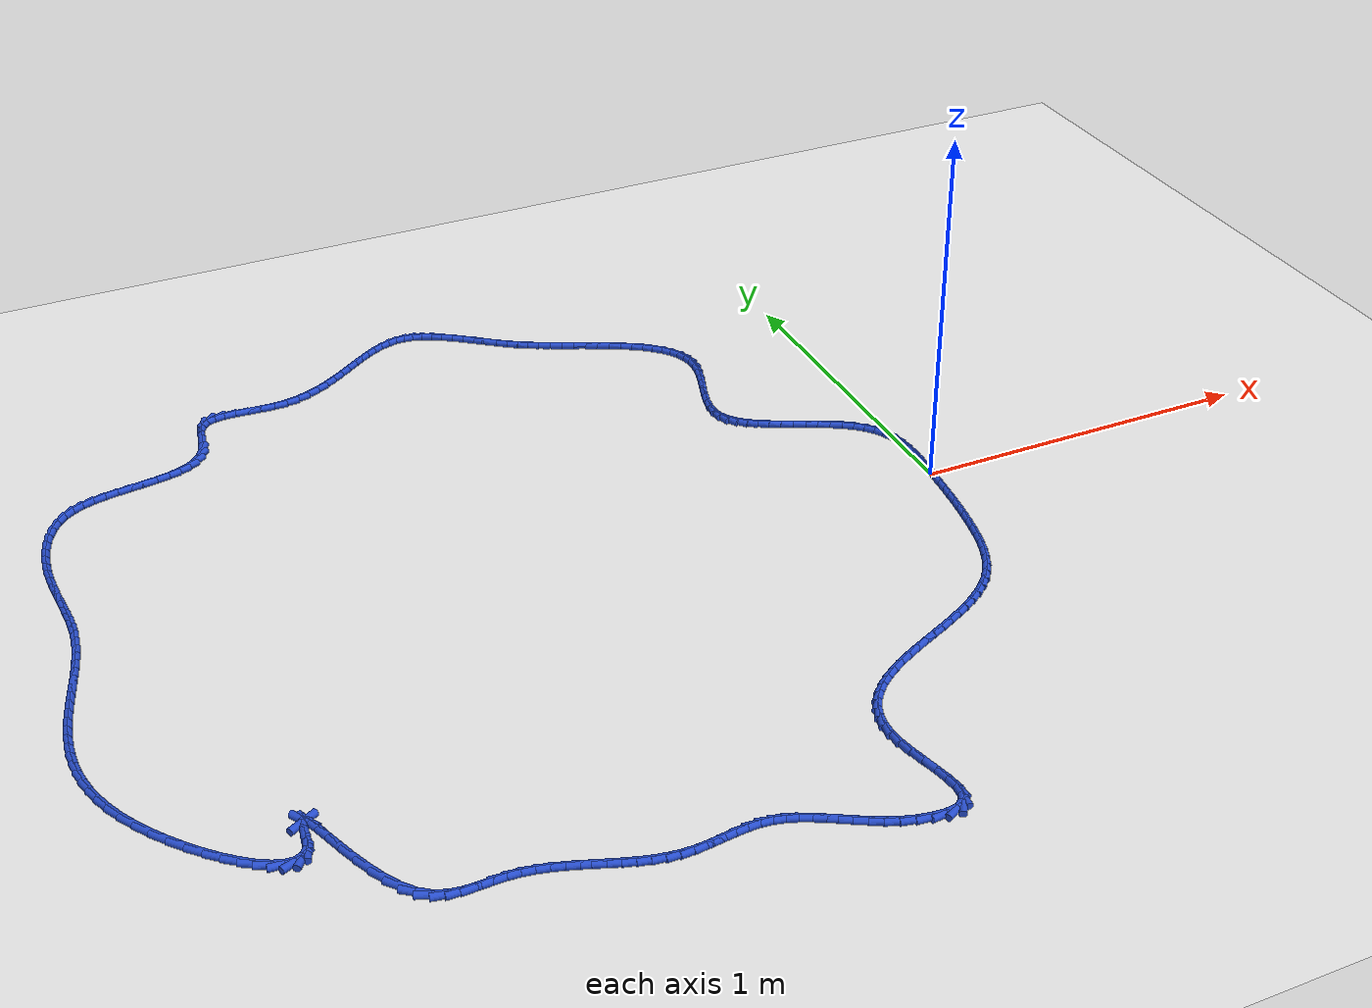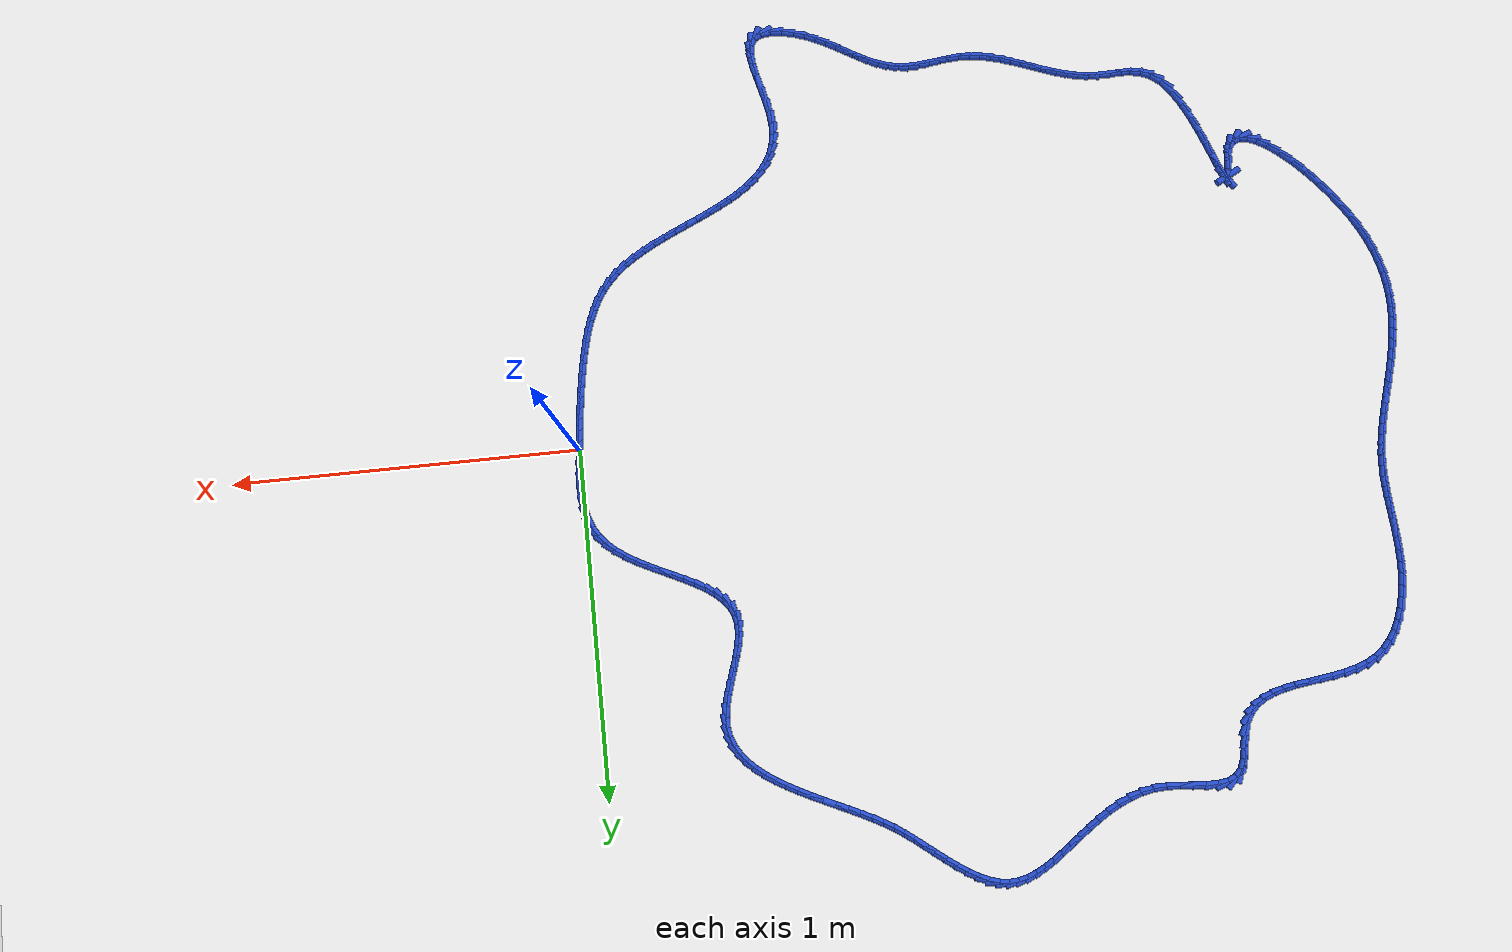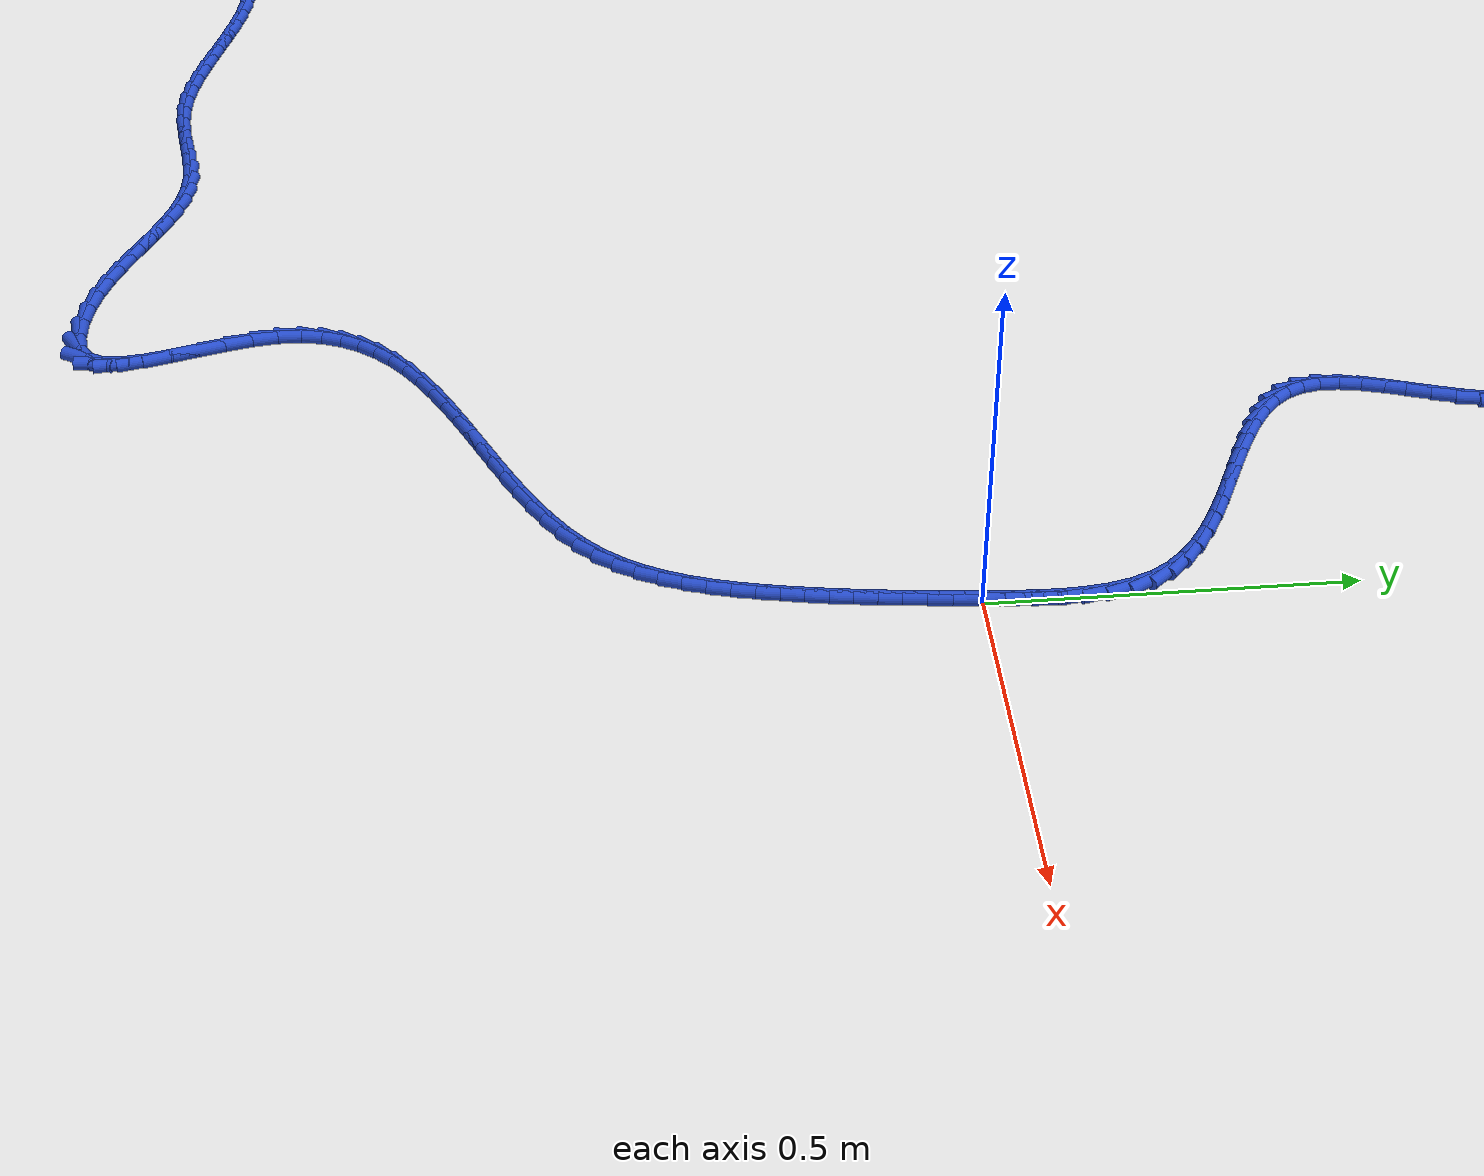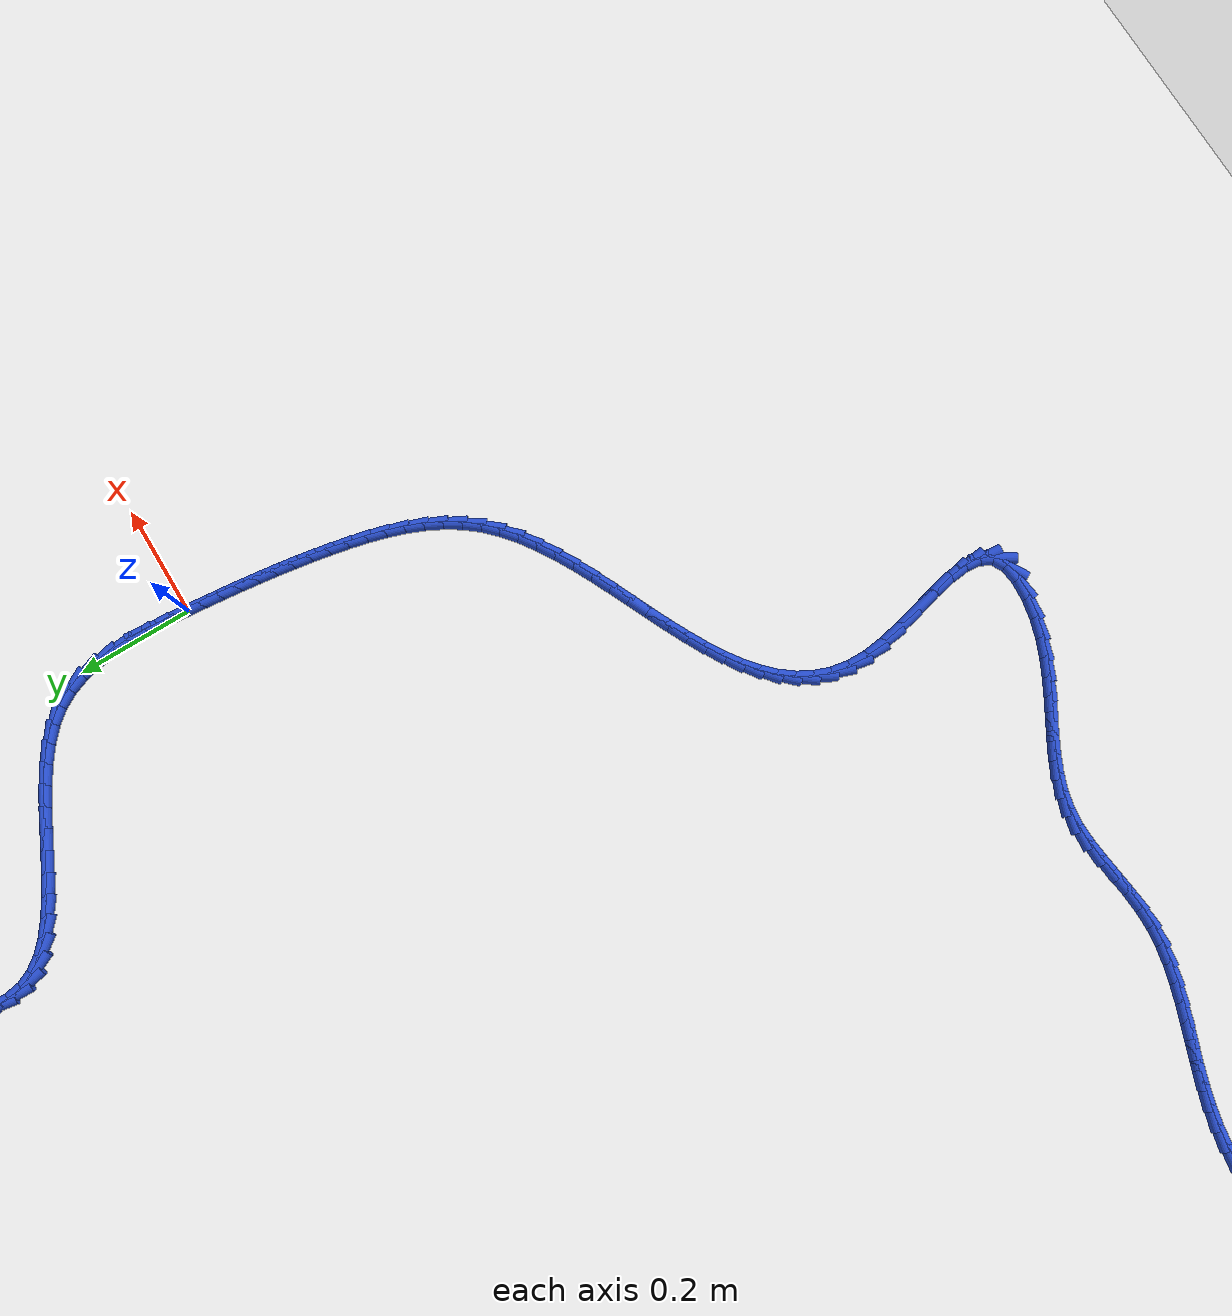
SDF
<sdf version="1.6">
 <world name="default">
  <light name="sun" type="directional">
   <pose>0 0 10 0 -0 0</pose>
   <diffuse>0.8 0.8 0.8 1</diffuse>
   <specular>0.2 0.2 0.2 1</specular>
   <attenuation>
    <range>1000</range>
    <constant>0.9</constant>
    <linear>0.01</linear>
    <quadratic>0.001</quadratic>
   </attenuation>
   <direction>-0.5 0.1 -0.9</direction>
  </light>
  <model name="ground_plane">
   <static>1</static>
   <link name="link">
    <collision name="collision">
     <geometry><plane><normal>0 0 1</normal><size>100 100</size></plane></geometry>
     <surface><friction><ode><mu>100</mu><mu2>50</mu2></ode></friction></surface>
    </collision>
    <visual name="visual">
     <cast_shadows>0</cast_shadows>
     <geometry><plane><normal>0 0 1</normal><size>100 100</size></plane></geometry>
     <material>
      <script><uri>file://media/materials/scripts/gazebo.material</uri><name>Gazebo/WhiteGlow</name></script>
     </material>
    </visual>
   </link>
  </model>
  <gravity>0 0 -9.8</gravity>
  <magnetic_field>6e-06 2.3e-05 -4.2e-05</magnetic_field>
  <atmosphere type="adiabatic"/>
  <physics name="default_physics" default="0" type="ode">
   <max_step_size>0.001</max_step_size>
   <real_time_factor>1</real_time_factor>
   <real_time_update_rate>1000</real_time_update_rate>
  </physics>
  <scene><ambient>0.4 0.4 0.4 1</ambient><background>0.7 0.7 0.7 1</background><shadows>1</shadows></scene>
  <spherical_coordinates>
   <surface_model>EARTH_WGS84</surface_model>
   <latitude_deg>0</latitude_deg>
   <longitude_deg>0</longitude_deg>
   <elevation>0</elevation>
   <heading_deg>0</heading_deg>
  </spherical_coordinates>
  <model name="line">
   <link name="link_0">
    <pose>-3.469446951953614e-18 6.245004513516506e-17 0.01 0 1.57 1.4901229241210485</pose>
    <collision name="collision">
     <geometry><cylinder><radius>0.01</radius><length>0.08</length></cylinder></geometry>
    </collision>
    <visual name="visual">
     <material>
      <script><name>Gazebo/Blue</name><uri>file://media/materials/scripts/gazebo.material</uri></script>
     </material>
     <geometry><cylinder><radius>0.01</radius><length>0.08</length></cylinder></geometry>
    </visual>
   </link>
   <link name="link_1">
    <pose>0.0027077996021664143 0.033492113431842434 0.01 0 1.57 1.5123215696676704</pose>
    <collision name="collision">
     <geometry><cylinder><radius>0.01</radius><length>0.08</length></cylinder></geometry>
    </collision>
    <visual name="visual">
     <material>
      <script><name>Gazebo/Blue</name><uri>file://media/materials/scripts/gazebo.material</uri></script>
     </material>
     <geometry><cylinder><radius>0.01</radius><length>0.08</length></cylinder></geometry>
    </visual>
   </link>
   <link name="link_2">
    <pose>0.004687725133957794 0.0673130040705249 0.01 0 1.57 1.552191958306774</pose>
    <collision name="collision">
     <geometry><cylinder><radius>0.01</radius><length>0.08</length></cylinder></geometry>
    </collision>
    <visual name="visual">
     <material>
      <script><name>Gazebo/Blue</name><uri>file://media/materials/scripts/gazebo.material</uri></script>
     </material>
     <geometry><cylinder><radius>0.01</radius><length>0.08</length></cylinder></geometry>
    </visual>
   </link>
   <link name="link_3">
    <pose>0.005314771219777069 0.10101335458900262 0.01 0 1.57 -1.5300456229993817</pose>
    <collision name="collision">
     <geometry><cylinder><radius>0.01</radius><length>0.08</length></cylinder></geometry>
    </collision>
    <visual name="visual">
     <material>
      <script><name>Gazebo/Blue</name><uri>file://media/materials/scripts/gazebo.material</uri></script>
     </material>
     <geometry><cylinder><radius>0.01</radius><length>0.08</length></cylinder></geometry>
    </visual>
   </link>
   <link name="link_4">
    <pose>0.003963932484027174 0.13414384766023082 0.01 0 1.57 -1.4482872086285352</pose>
    <collision name="collision">
     <geometry><cylinder><radius>0.01</radius><length>0.08</length></cylinder></geometry>
    </collision>
    <visual name="visual">
     <material>
      <script><name>Gazebo/Blue</name><uri>file://media/materials/scripts/gazebo.material</uri></script>
     </material>
     <geometry><cylinder><radius>0.01</radius><length>0.08</length></cylinder></geometry>
    </visual>
   </link>
   <link name="link_5">
    <pose>1.0203551111035575e-05 0.16625516595716458 0.01 0 1.57 -1.34058564515871</pose>
    <collision name="collision">
     <geometry><cylinder><radius>0.01</radius><length>0.08</length></cylinder></geometry>
    </collision>
    <visual name="visual">
     <material>
      <script><name>Gazebo/Blue</name><uri>file://media/materials/scripts/gazebo.material</uri></script>
     </material>
     <geometry><cylinder><radius>0.01</radius><length>0.08</length></cylinder></geometry>
    </visual>
   </link>
   <link name="link_6">
    <pose>-0.00717142095456841 0.19689799215275902 0.01 0 1.57 -1.2040337244505515</pose>
    <collision name="collision">
     <geometry><cylinder><radius>0.01</radius><length>0.08</length></cylinder></geometry>
    </collision>
    <visual name="visual">
     <material>
      <script><name>Gazebo/Blue</name><uri>file://media/materials/scripts/gazebo.material</uri></script>
     </material>
     <geometry><cylinder><radius>0.01</radius><length>0.08</length></cylinder></geometry>
    </visual>
   </link>
   <link name="link_7">
    <pose>-0.018205946408608238 0.22562300891996945 0.01 0 1.57 -1.0388727572746694</pose>
    <collision name="collision">
     <geometry><cylinder><radius>0.01</radius><length>0.08</length></cylinder></geometry>
    </collision>
    <visual name="visual">
     <material>
      <script><name>Gazebo/Blue</name><uri>file://media/materials/scripts/gazebo.material</uri></script>
     </material>
     <geometry><cylinder><radius>0.01</radius><length>0.08</length></cylinder></geometry>
    </visual>
   </link>
   <link name="link_8">
    <pose>-0.0337178486407541 0.2519812085701402 0.01 0 1.57 -0.8640773350608283</pose>
    <collision name="collision">
     <geometry><cylinder><radius>0.01</radius><length>0.08</length></cylinder></geometry>
    </collision>
    <visual name="visual">
     <material>
      <script><name>Gazebo/Blue</name><uri>file://media/materials/scripts/gazebo.material</uri></script>
     </material>
     <geometry><cylinder><radius>0.01</radius><length>0.08</length></cylinder></geometry>
    </visual>
   </link>
   <link name="link_9">
    <pose>-0.0539898748152464 0.27572340050943794 0.01 0 1.57 -0.7207456461678292</pose>
    <collision name="collision">
     <geometry><cylinder><radius>0.01</radius><length>0.08</length></cylinder></geometry>
    </collision>
    <visual name="visual">
     <material>
      <script><name>Gazebo/Blue</name><uri>file://media/materials/scripts/gazebo.material</uri></script>
     </material>
     <geometry><cylinder><radius>0.01</radius><length>0.08</length></cylinder></geometry>
    </visual>
   </link>
   <link name="link_10">
    <pose>-0.07837571957989971 0.29714363383536285 0.01 0 1.57 -0.613045753282592</pose>
    <collision name="collision">
     <geometry><cylinder><radius>0.01</radius><length>0.08</length></cylinder></geometry>
    </collision>
    <visual name="visual">
     <material>
      <script><name>Gazebo/Blue</name><uri>file://media/materials/scripts/gazebo.material</uri></script>
     </material>
     <geometry><cylinder><radius>0.01</radius><length>0.08</length></cylinder></geometry>
    </visual>
   </link>
   <link name="link_11">
    <pose>-0.10607268852153606 0.3166274021479808 0.01 0 1.57 -0.5357706391768827</pose>
    <collision name="collision">
     <geometry><cylinder><radius>0.01</radius><length>0.08</length></cylinder></geometry>
    </collision>
    <visual name="visual">
     <material>
      <script><name>Gazebo/Blue</name><uri>file://media/materials/scripts/gazebo.material</uri></script>
     </material>
     <geometry><cylinder><radius>0.01</radius><length>0.08</length></cylinder></geometry>
    </visual>
   </link>
   <link name="link_12">
    <pose>-0.13627808722697748 0.3345601990473574 0.01 0 1.57 -0.4837902180100879</pose>
    <collision name="collision">
     <geometry><cylinder><radius>0.01</radius><length>0.08</length></cylinder></geometry>
    </collision>
    <visual name="visual">
     <material>
      <script><name>Gazebo/Blue</name><uri>file://media/materials/scripts/gazebo.material</uri></script>
     </material>
     <geometry><cylinder><radius>0.01</radius><length>0.08</length></cylinder></geometry>
    </visual>
   </link>
   <link name="link_13">
    <pose>-0.168189221283046 0.35132751813355845 0.01 0 1.57 -0.45336189439639357</pose>
    <collision name="collision">
     <geometry><cylinder><radius>0.01</radius><length>0.08</length></cylinder></geometry>
    </collision>
    <visual name="visual">
     <material>
      <script><name>Gazebo/Blue</name><uri>file://media/materials/scripts/gazebo.material</uri></script>
     </material>
     <geometry><cylinder><radius>0.01</radius><length>0.08</length></cylinder></geometry>
    </visual>
   </link>
   <link name="link_14">
    <pose>-0.20100339627656347 0.3673148530066496 0.01 0 1.57 -0.44241777368802937</pose>
    <collision name="collision">
     <geometry><cylinder><radius>0.01</radius><length>0.08</length></cylinder></geometry>
    </collision>
    <visual name="visual">
     <material>
      <script><name>Gazebo/Blue</name><uri>file://media/materials/scripts/gazebo.material</uri></script>
     </material>
     <geometry><cylinder><radius>0.01</radius><length>0.08</length></cylinder></geometry>
    </visual>
   </link>
   <link name="link_15">
    <pose>-0.23391791779435206 0.3829076972666967 0.01 0 1.57 -0.45059369855419107</pose>
    <collision name="collision">
     <geometry><cylinder><radius>0.01</radius><length>0.08</length></cylinder></geometry>
    </collision>
    <visual name="visual">
     <material>
      <script><name>Gazebo/Blue</name><uri>file://media/materials/scripts/gazebo.material</uri></script>
     </material>
     <geometry><cylinder><radius>0.01</radius><length>0.08</length></cylinder></geometry>
    </visual>
   </link>
   <link name="link_16">
    <pose>-0.2661300914232338 0.3984915445137655 0.01 0 1.57 -0.4793304913111755</pose>
    <collision name="collision">
     <geometry><cylinder><radius>0.01</radius><length>0.08</length></cylinder></geometry>
    </collision>
    <visual name="visual">
     <material>
      <script><name>Gazebo/Blue</name><uri>file://media/materials/scripts/gazebo.material</uri></script>
     </material>
     <geometry><cylinder><radius>0.01</radius><length>0.08</length></cylinder></geometry>
    </visual>
   </link>
   <link name="link_17">
    <pose>-0.2968372227500305 0.4144518883479217 0.01 0 1.57 -0.5321636464782197</pose>
    <collision name="collision">
     <geometry><cylinder><radius>0.01</radius><length>0.08</length></cylinder></geometry>
    </collision>
    <visual name="visual">
     <material>
      <script><name>Gazebo/Blue</name><uri>file://media/materials/scripts/gazebo.material</uri></script>
     </material>
     <geometry><cylinder><radius>0.01</radius><length>0.08</length></cylinder></geometry>
    </visual>
   </link>
   <link name="link_18">
    <pose>-0.32523661736156423 0.431174222369231 0.01 0 1.57 -0.6151585534215233</pose>
    <collision name="collision">
     <geometry><cylinder><radius>0.01</radius><length>0.08</length></cylinder></geometry>
    </collision>
    <visual name="visual">
     <material>
      <script><name>Gazebo/Blue</name><uri>file://media/materials/scripts/gazebo.material</uri></script>
     </material>
     <geometry><cylinder><radius>0.01</radius><length>0.08</length></cylinder></geometry>
    </visual>
   </link>
   <link name="link_19">
    <pose>-0.35052558084465696 0.4490440401777591 0.01 0 1.57 -0.7370516372920425</pose>
    <collision name="collision">
     <geometry><cylinder><radius>0.01</radius><length>0.08</length></cylinder></geometry>
    </collision>
    <visual name="visual">
     <material>
      <script><name>Gazebo/Blue</name><uri>file://media/materials/scripts/gazebo.material</uri></script>
     </material>
     <geometry><cylinder><radius>0.01</radius><length>0.08</length></cylinder></geometry>
    </visual>
   </link>
   <link name="link_20">
    <pose>-0.3719014187861311 0.468446835373572 0.01 0 1.57 -0.9075124071370088</pose>
    <collision name="collision">
     <geometry><cylinder><radius>0.01</radius><length>0.08</length></cylinder></geometry>
    </collision>
    <visual name="visual">
     <material>
      <script><name>Gazebo/Blue</name><uri>file://media/materials/scripts/gazebo.material</uri></script>
     </material>
     <geometry><cylinder><radius>0.01</radius><length>0.08</length></cylinder></geometry>
    </visual>
   </link>
   <link name="link_21">
    <pose>-0.3885614367728081 0.4897681015567351 0.01 0 1.57 -1.1301311127968117</pose>
    <collision name="collision">
     <geometry><cylinder><radius>0.01</radius><length>0.08</length></cylinder></geometry>
    </collision>
    <visual name="visual">
     <material>
      <script><name>Gazebo/Blue</name><uri>file://media/materials/scripts/gazebo.material</uri></script>
     </material>
     <geometry><cylinder><radius>0.01</radius><length>0.08</length></cylinder></geometry>
    </visual>
   </link>
   <link name="link_22">
    <pose>-0.3997029403915102 0.5133933323273143 0.01 0 1.57 -1.3850555490013627</pose>
    <collision name="collision">
     <geometry><cylinder><radius>0.01</radius><length>0.08</length></cylinder></geometry>
    </collision>
    <visual name="visual">
     <material>
      <script><name>Gazebo/Blue</name><uri>file://media/materials/scripts/gazebo.material</uri></script>
     </material>
     <geometry><cylinder><radius>0.01</radius><length>0.08</length></cylinder></geometry>
    </visual>
   </link>
   <link name="link_23">
    <pose>-0.4046382467985747 0.5396580011457781 0.01 0 1.57 1.5450411678632596</pose>
    <collision name="collision">
     <geometry><cylinder><radius>0.01</radius><length>0.08</length></cylinder></geometry>
    </collision>
    <visual name="visual">
     <material>
      <script><name>Gazebo/Blue</name><uri>file://media/materials/scripts/gazebo.material</uri></script>
     </material>
     <geometry><cylinder><radius>0.01</radius><length>0.08</length></cylinder></geometry>
    </visual>
   </link>
   <link name="link_24">
    <pose>-0.4038986675206872 0.5683674237777615 0.01 0 1.57 1.404294627243829</pose>
    <collision name="collision">
     <geometry><cylinder><radius>0.01</radius><length>0.08</length></cylinder></geometry>
    </collision>
    <visual name="visual">
     <material>
      <script><name>Gazebo/Blue</name><uri>file://media/materials/scripts/gazebo.material</uri></script>
     </material>
     <geometry><cylinder><radius>0.01</radius><length>0.08</length></cylinder></geometry>
    </visual>
   </link>
   <link name="link_25">
    <pose>-0.3987493246039748 0.5990077715343443 0.01 0 1.57 1.317886489785513</pose>
    <collision name="collision">
     <geometry><cylinder><radius>0.01</radius><length>0.08</length></cylinder></geometry>
    </collision>
    <visual name="visual">
     <material>
      <script><name>Gazebo/Blue</name><uri>file://media/materials/scripts/gazebo.material</uri></script>
     </material>
     <geometry><cylinder><radius>0.01</radius><length>0.08</length></cylinder></geometry>
    </visual>
   </link>
   <link name="link_26">
    <pose>-0.39046540892263387 0.6310608366525033 0.01 0 1.57 1.2721426269081333</pose>
    <collision name="collision">
     <geometry><cylinder><radius>0.01</radius><length>0.08</length></cylinder></geometry>
    </collision>
    <visual name="visual">
     <material>
      <script><name>Gazebo/Blue</name><uri>file://media/materials/scripts/gazebo.material</uri></script>
     </material>
     <geometry><cylinder><radius>0.01</radius><length>0.08</length></cylinder></geometry>
    </visual>
   </link>
   <link name="link_27">
    <pose>-0.3803221113508607 0.6640084113692152 0.01 0 1.57 1.2593563363764915</pose>
    <collision name="collision">
     <geometry><cylinder><radius>0.01</radius><length>0.08</length></cylinder></geometry>
    </collision>
    <visual name="visual">
     <material>
      <script><name>Gazebo/Blue</name><uri>file://media/materials/scripts/gazebo.material</uri></script>
     </material>
     <geometry><cylinder><radius>0.01</radius><length>0.08</length></cylinder></geometry>
    </visual>
   </link>
   <link name="link_28">
    <pose>-0.3695946227628511 0.6973322879214572 0.01 0 1.57 1.277076730391057</pose>
    <collision name="collision">
     <geometry><cylinder><radius>0.01</radius><length>0.08</length></cylinder></geometry>
    </collision>
    <visual name="visual">
     <material>
      <script><name>Gazebo/Blue</name><uri>file://media/materials/scripts/gazebo.material</uri></script>
     </material>
     <geometry><cylinder><radius>0.01</radius><length>0.08</length></cylinder></geometry>
    </visual>
   </link>
   <link name="link_29">
    <pose>-0.3595581340328015 0.7305142585462057 0.01 0 1.57 1.3275596198123802</pose>
    <collision name="collision">
     <geometry><cylinder><radius>0.01</radius><length>0.08</length></cylinder></geometry>
    </collision>
    <visual name="visual">
     <material>
      <script><name>Gazebo/Blue</name><uri>file://media/materials/scripts/gazebo.material</uri></script>
     </material>
     <geometry><cylinder><radius>0.01</radius><length>0.08</length></cylinder></geometry>
    </visual>
   </link>
   <link name="link_30">
    <pose>-0.35148783603490813 0.7630361154804376 0.01 0 1.57 1.4179340109638274</pose>
    <collision name="collision">
     <geometry><cylinder><radius>0.01</radius><length>0.08</length></cylinder></geometry>
    </collision>
    <visual name="visual">
     <material>
      <script><name>Gazebo/Blue</name><uri>file://media/materials/scripts/gazebo.material</uri></script>
     </material>
     <geometry><cylinder><radius>0.01</radius><length>0.08</length></cylinder></geometry>
    </visual>
   </link>
   <link name="link_31">
    <pose>-0.3466589196433672 0.7943796509611301 0.01 0 1.57 1.5601558338305195</pose>
    <collision name="collision">
     <geometry><cylinder><radius>0.01</radius><length>0.08</length></cylinder></geometry>
    </collision>
    <visual name="visual">
     <material>
      <script><name>Gazebo/Blue</name><uri>file://media/materials/scripts/gazebo.material</uri></script>
     </material>
     <geometry><cylinder><radius>0.01</radius><length>0.08</length></cylinder></geometry>
    </visual>
   </link>
   <link name="link_32">
    <pose>-0.34634343589949235 0.8240278861016566 0.01 0 1.57 -1.3934364828090906</pose>
    <collision name="collision">
     <geometry><cylinder><radius>0.01</radius><length>0.08</length></cylinder></geometry>
    </collision>
    <visual name="visual">
     <material>
      <script><name>Gazebo/Blue</name><uri>file://media/materials/scripts/gazebo.material</uri></script>
     </material>
     <geometry><cylinder><radius>0.01</radius><length>0.08</length></cylinder></geometry>
    </visual>
   </link>
   <link name="link_33">
    <pose>-0.3512973506692962 0.8516658288454583 0.01 0 1.57 -1.2037991851993026</pose>
    <collision name="collision">
     <geometry><cylinder><radius>0.01</radius><length>0.08</length></cylinder></geometry>
    </collision>
    <visual name="visual">
     <material>
      <script><name>Gazebo/Blue</name><uri>file://media/materials/scripts/gazebo.material</uri></script>
     </material>
     <geometry><cylinder><radius>0.01</radius><length>0.08</length></cylinder></geometry>
    </visual>
   </link>
   <link name="link_34">
    <pose>-0.36119116542394997 0.877403319165179 0.01 0 1.57 -1.031396989596992</pose>
    <collision name="collision">
     <geometry><cylinder><radius>0.01</radius><length>0.08</length></cylinder></geometry>
    </collision>
    <visual name="visual">
     <material>
      <script><name>Gazebo/Blue</name><uri>file://media/materials/scripts/gazebo.material</uri></script>
     </material>
     <geometry><cylinder><radius>0.01</radius><length>0.08</length></cylinder></geometry>
    </visual>
   </link>
   <link name="link_35">
    <pose>-0.375558222609207 0.9014038787086686 0.01 0 1.57 -0.8844219875120721</pose>
    <collision name="collision">
     <geometry><cylinder><radius>0.01</radius><length>0.08</length></cylinder></geometry>
    </collision>
    <visual name="visual">
     <material>
      <script><name>Gazebo/Blue</name><uri>file://media/materials/scripts/gazebo.material</uri></script>
     </material>
     <geometry><cylinder><radius>0.01</radius><length>0.08</length></cylinder></geometry>
    </visual>
   </link>
   <link name="link_36">
    <pose>-0.3939318646708209 0.9238310291237766 0.01 0 1.57 -0.7645232768600436</pose>
    <collision name="collision">
     <geometry><cylinder><radius>0.01</radius><length>0.08</length></cylinder></geometry>
    </collision>
    <visual name="visual">
     <material>
      <script><name>Gazebo/Blue</name><uri>file://media/materials/scripts/gazebo.material</uri></script>
     </material>
     <geometry><cylinder><radius>0.01</radius><length>0.08</length></cylinder></geometry>
    </visual>
   </link>
   <link name="link_37">
    <pose>-0.4158454340545449 0.9448482920583526 0.01 0 1.57 -0.6693842491865951</pose>
    <collision name="collision">
     <geometry><cylinder><radius>0.01</radius><length>0.08</length></cylinder></geometry>
    </collision>
    <visual name="visual">
     <material>
      <script><name>Gazebo/Blue</name><uri>file://media/materials/scripts/gazebo.material</uri></script>
     </material>
     <geometry><cylinder><radius>0.01</radius><length>0.08</length></cylinder></geometry>
    </visual>
   </link>
   <link name="link_38">
    <pose>-0.4408322732061327 0.9646191891602467 0.01 0 1.57 -0.5953034214540748</pose>
    <collision name="collision">
     <geometry><cylinder><radius>0.01</radius><length>0.08</length></cylinder></geometry>
    </collision>
    <visual name="visual">
     <material>
      <script><name>Gazebo/Blue</name><uri>file://media/materials/scripts/gazebo.material</uri></script>
     </material>
     <geometry><cylinder><radius>0.01</radius><length>0.08</length></cylinder></geometry>
    </visual>
   </link>
   <link name="link_39">
    <pose>-0.4684257245713378 0.9833072420773088 0.01 0 1.57 -0.5386540889914756</pose>
    <collision name="collision">
     <geometry><cylinder><radius>0.01</radius><length>0.08</length></cylinder></geometry>
    </collision>
    <visual name="visual">
     <material>
      <script><name>Gazebo/Blue</name><uri>file://media/materials/scripts/gazebo.material</uri></script>
     </material>
     <geometry><cylinder><radius>0.01</radius><length>0.08</length></cylinder></geometry>
    </visual>
   </link>
   <link name="link_40">
    <pose>-0.4981591305959136 1.0010759724573883 0.01 0 1.57 -0.49644651626106195</pose>
    <collision name="collision">
     <geometry><cylinder><radius>0.01</radius><length>0.08</length></cylinder></geometry>
    </collision>
    <visual name="visual">
     <material>
      <script><name>Gazebo/Blue</name><uri>file://media/materials/scripts/gazebo.material</uri></script>
     </material>
     <geometry><cylinder><radius>0.01</radius><length>0.08</length></cylinder></geometry>
    </visual>
   </link>
   <link name="link_41">
    <pose>-0.5295658337256136 1.0180889019483355 0.01 0 1.57 -0.4664395828567263</pose>
    <collision name="collision">
     <geometry><cylinder><radius>0.01</radius><length>0.08</length></cylinder></geometry>
    </collision>
    <visual name="visual">
     <material>
      <script><name>Gazebo/Blue</name><uri>file://media/materials/scripts/gazebo.material</uri></script>
     </material>
     <geometry><cylinder><radius>0.01</radius><length>0.08</length></cylinder></geometry>
    </visual>
   </link>
   <link name="link_42">
    <pose>-0.562179176406191 1.0345095521979994 0.01 0 1.57 -0.4470884998388332</pose>
    <collision name="collision">
     <geometry><cylinder><radius>0.01</radius><length>0.08</length></cylinder></geometry>
    </collision>
    <visual name="visual">
     <material>
      <script><name>Gazebo/Blue</name><uri>file://media/materials/scripts/gazebo.material</uri></script>
     </material>
     <geometry><cylinder><radius>0.01</radius><length>0.08</length></cylinder></geometry>
    </visual>
   </link>
   <link name="link_43">
    <pose>-0.5955325010833996 1.0505014448542305 0.01 0 1.57 -0.43746250256236646</pose>
    <collision name="collision">
     <geometry><cylinder><radius>0.01</radius><length>0.08</length></cylinder></geometry>
    </collision>
    <visual name="visual">
     <material>
      <script><name>Gazebo/Blue</name><uri>file://media/materials/scripts/gazebo.material</uri></script>
     </material>
     <geometry><cylinder><radius>0.01</radius><length>0.08</length></cylinder></geometry>
    </visual>
   </link>
   <link name="link_44">
    <pose>-0.6291591502029924 1.0662281015648778 0.01 0 1.57 -0.43718525185235146</pose>
    <collision name="collision">
     <geometry><cylinder><radius>0.01</radius><length>0.08</length></cylinder></geometry>
    </collision>
    <visual name="visual">
     <material>
      <script><name>Gazebo/Blue</name><uri>file://media/materials/scripts/gazebo.material</uri></script>
     </material>
     <geometry><cylinder><radius>0.01</radius><length>0.08</length></cylinder></geometry>
    </visual>
   </link>
   <link name="link_45">
    <pose>-0.6625924662107235 1.0818530439777918 0.01 0 1.57 -0.4464171683865246</pose>
    <collision name="collision">
     <geometry><cylinder><radius>0.01</radius><length>0.08</length></cylinder></geometry>
    </collision>
    <visual name="visual">
     <material>
      <script><name>Gazebo/Blue</name><uri>file://media/materials/scripts/gazebo.material</uri></script>
     </material>
     <geometry><cylinder><radius>0.01</radius><length>0.08</length></cylinder></geometry>
    </visual>
   </link>
   <link name="link_46">
    <pose>-0.6953657915523462 1.097539793740822 0.01 0 1.57 -0.46588836568821995</pose>
    <collision name="collision">
     <geometry><cylinder><radius>0.01</radius><length>0.08</length></cylinder></geometry>
    </collision>
    <visual name="visual">
     <material>
      <script><name>Gazebo/Blue</name><uri>file://media/materials/scripts/gazebo.material</uri></script>
     </material>
     <geometry><cylinder><radius>0.01</radius><length>0.08</length></cylinder></geometry>
    </visual>
   </link>
   <link name="link_47">
    <pose>-0.7270124686736137 1.113451872501818 0.01 0 1.57 -0.4969890652003907</pose>
    <collision name="collision">
     <geometry><cylinder><radius>0.01</radius><length>0.08</length></cylinder></geometry>
    </collision>
    <visual name="visual">
     <material>
      <script><name>Gazebo/Blue</name><uri>file://media/materials/scripts/gazebo.material</uri></script>
     </material>
     <geometry><cylinder><radius>0.01</radius><length>0.08</length></cylinder></geometry>
    </visual>
   </link>
   <link name="link_48">
    <pose>-0.7570658400202797 1.12975280190863 0.01 0 1.57 -0.5416075769836707</pose>
    <collision name="collision">
     <geometry><cylinder><radius>0.01</radius><length>0.08</length></cylinder></geometry>
    </collision>
    <visual name="visual">
     <material>
      <script><name>Gazebo/Blue</name><uri>file://media/materials/scripts/gazebo.material</uri></script>
     </material>
     <geometry><cylinder><radius>0.01</radius><length>0.08</length></cylinder></geometry>
    </visual>
   </link>
   <link name="link_49">
    <pose>-0.7850832771548926 1.1466085666402683 0.01 0 1.57 -0.5915583991998784</pose>
    <collision name="collision">
     <geometry><cylinder><radius>0.01</radius><length>0.08</length></cylinder></geometry>
    </collision>
    <visual name="visual">
     <material>
      <script><name>Gazebo/Blue</name><uri>file://media/materials/scripts/gazebo.material</uri></script>
     </material>
     <geometry><cylinder><radius>0.01</radius><length>0.08</length></cylinder></geometry>
    </visual>
   </link>
   <link name="link_50">
    <pose>-0.811358450700799 1.1642606234601167 0.01 0 1.57 -0.6313274630269666</pose>
    <collision name="collision">
     <geometry><cylinder><radius>0.01</radius><length>0.08</length></cylinder></geometry>
    </collision>
    <visual name="visual">
     <material>
      <script><name>Gazebo/Blue</name><uri>file://media/materials/scripts/gazebo.material</uri></script>
     </material>
     <geometry><cylinder><radius>0.01</radius><length>0.08</length></cylinder></geometry>
    </visual>
   </link>
   <link name="link_51">
    <pose>-0.8370406054537128 1.1830381271466242 0.01 0 1.57 -0.6558054911247395</pose>
    <collision name="collision">
     <geometry><cylinder><radius>0.01</radius><length>0.08</length></cylinder></geometry>
    </collision>
    <visual name="visual">
     <material>
      <script><name>Gazebo/Blue</name><uri>file://media/materials/scripts/gazebo.material</uri></script>
     </material>
     <geometry><cylinder><radius>0.01</radius><length>0.08</length></cylinder></geometry>
    </visual>
   </link>
   <link name="link_52">
    <pose>-0.86319304337328 1.2031599608446233 0.01 0 1.57 -0.6629031661865104</pose>
    <collision name="collision">
     <geometry><cylinder><radius>0.01</radius><length>0.08</length></cylinder></geometry>
    </collision>
    <visual name="visual">
     <material>
      <script><name>Gazebo/Blue</name><uri>file://media/materials/scripts/gazebo.material</uri></script>
     </material>
     <geometry><cylinder><radius>0.01</radius><length>0.08</length></cylinder></geometry>
    </visual>
   </link>
   <link name="link_53">
    <pose>-0.8900087199813189 1.2240967639176559 0.01 0 1.57 -0.6535054408481771</pose>
    <collision name="collision">
     <geometry><cylinder><radius>0.01</radius><length>0.08</length></cylinder></geometry>
    </collision>
    <visual name="visual">
     <material>
      <script><name>Gazebo/Blue</name><uri>file://media/materials/scripts/gazebo.material</uri></script>
     </material>
     <geometry><cylinder><radius>0.01</radius><length>0.08</length></cylinder></geometry>
    </visual>
   </link>
   <link name="link_54">
    <pose>-0.917332948392003 1.245020304775895 0.01 0 1.57 -0.6276705999102542</pose>
    <collision name="collision">
     <geometry><cylinder><radius>0.01</radius><length>0.08</length></cylinder></geometry>
    </collision>
    <visual name="visual">
     <material>
      <script><name>Gazebo/Blue</name><uri>file://media/materials/scripts/gazebo.material</uri></script>
     </material>
     <geometry><cylinder><radius>0.01</radius><length>0.08</length></cylinder></geometry>
    </visual>
   </link>
   <link name="link_55">
    <pose>-0.945010130816856 1.265101568719234 0.01 0 1.57 -0.5836922269840704</pose>
    <collision name="collision">
     <geometry><cylinder><radius>0.01</radius><length>0.08</length></cylinder></geometry>
    </collision>
    <visual name="visual">
     <material>
      <script><name>Gazebo/Blue</name><uri>file://media/materials/scripts/gazebo.material</uri></script>
     </material>
     <geometry><cylinder><radius>0.01</radius><length>0.08</length></cylinder></geometry>
    </visual>
   </link>
   <link name="link_56">
    <pose>-0.9728846694674023 1.2835115410475668 0.01 0 1.57 -0.5179975986065161</pose>
    <collision name="collision">
     <geometry><cylinder><radius>0.01</radius><length>0.08</length></cylinder></geometry>
    </collision>
    <visual name="visual">
     <material>
      <script><name>Gazebo/Blue</name><uri>file://media/materials/scripts/gazebo.material</uri></script>
     </material>
     <geometry><cylinder><radius>0.01</radius><length>0.08</length></cylinder></geometry>
    </visual>
   </link>
   <link name="link_57">
    <pose>-1.0008009665551656 1.2994212070607873 0.01 0 1.57 -0.42492300689233686</pose>
    <collision name="collision">
     <geometry><cylinder><radius>0.01</radius><length>0.08</length></cylinder></geometry>
    </collision>
    <visual name="visual">
     <material>
      <script><name>Gazebo/Blue</name><uri>file://media/materials/scripts/gazebo.material</uri></script>
     </material>
     <geometry><cylinder><radius>0.01</radius><length>0.08</length></cylinder></geometry>
    </visual>
   </link>
   <link name="link_58">
    <pose>-1.0286034242916702 1.312001552058789 0.01 0 1.57 -0.29684946125277933</pose>
    <collision name="collision">
     <geometry><cylinder><radius>0.01</radius><length>0.08</length></cylinder></geometry>
    </collision>
    <visual name="visual">
     <material>
      <script><name>Gazebo/Blue</name><uri>file://media/materials/scripts/gazebo.material</uri></script>
     </material>
     <geometry><cylinder><radius>0.01</radius><length>0.08</length></cylinder></geometry>
    </visual>
   </link>
   <link name="link_59">
    <pose>-1.0561364448884396 1.3204235613414648 0.01 0 1.57 -0.12661109981821145</pose>
    <collision name="collision">
     <geometry><cylinder><radius>0.01</radius><length>0.08</length></cylinder></geometry>
    </collision>
    <visual name="visual">
     <material>
      <script><name>Gazebo/Blue</name><uri>file://media/materials/scripts/gazebo.material</uri></script>
     </material>
     <geometry><cylinder><radius>0.01</radius><length>0.08</length></cylinder></geometry>
    </visual>
   </link>
   <link name="link_60">
    <pose>-1.083247722461375 1.3238746102809726 0.01 0 1.57 0.064274413914057</pose>
    <collision name="collision">
     <geometry><cylinder><radius>0.01</radius><length>0.08</length></cylinder></geometry>
    </collision>
    <visual name="visual">
     <material>
      <script><name>Gazebo/Blue</name><uri>file://media/materials/scripts/gazebo.material</uri></script>
     </material>
     <geometry><cylinder><radius>0.01</radius><length>0.08</length></cylinder></geometry>
    </visual>
   </link>
   <link name="link_61">
    <pose>-1.1099087832845687 1.3221586225414899 0.01 0 1.57 0.23439953047738915</pose>
    <collision name="collision">
     <geometry><cylinder><radius>0.01</radius><length>0.08</length></cylinder></geometry>
    </collision>
    <visual name="visual">
     <material>
      <script><name>Gazebo/Blue</name><uri>file://media/materials/scripts/gazebo.material</uri></script>
     </material>
     <geometry><cylinder><radius>0.01</radius><length>0.08</length></cylinder></geometry>
    </visual>
   </link>
   <link name="link_62">
    <pose>-1.136249660738163 1.3158687132778153 0.01 0 1.57 0.3723971614312031</pose>
    <collision name="collision">
     <geometry><cylinder><radius>0.01</radius><length>0.08</length></cylinder></geometry>
    </collision>
    <visual name="visual">
     <material>
      <script><name>Gazebo/Blue</name><uri>file://media/materials/scripts/gazebo.material</uri></script>
     </material>
     <geometry><cylinder><radius>0.01</radius><length>0.08</length></cylinder></geometry>
    </visual>
   </link>
   <link name="link_63">
    <pose>-1.1624107478600412 1.3056495773747598 0.01 0 1.57 0.4771172926010642</pose>
    <collision name="collision">
     <geometry><cylinder><radius>0.01</radius><length>0.08</length></cylinder></geometry>
    </collision>
    <visual name="visual">
     <material>
      <script><name>Gazebo/Blue</name><uri>file://media/materials/scripts/gazebo.material</uri></script>
     </material>
     <geometry><cylinder><radius>0.01</radius><length>0.08</length></cylinder></geometry>
    </visual>
   </link>
   <link name="link_64">
    <pose>-1.1885324376880875 1.292145909717135 0.01 0 1.57 0.5518338476270463</pose>
    <collision name="collision">
     <geometry><cylinder><radius>0.01</radius><length>0.08</length></cylinder></geometry>
    </collision>
    <visual name="visual">
     <material>
      <script><name>Gazebo/Blue</name><uri>file://media/materials/scripts/gazebo.material</uri></script>
     </material>
     <geometry><cylinder><radius>0.01</radius><length>0.08</length></cylinder></geometry>
    </visual>
   </link>
   <link name="link_65">
    <pose>-1.2147551232601854 1.2760024051897512 0.01 0 1.57 0.6008643223450567</pose>
    <collision name="collision">
     <geometry><cylinder><radius>0.01</radius><length>0.08</length></cylinder></geometry>
    </collision>
    <visual name="visual">
     <material>
      <script><name>Gazebo/Blue</name><uri>file://media/materials/scripts/gazebo.material</uri></script>
     </material>
     <geometry><cylinder><radius>0.01</radius><length>0.08</length></cylinder></geometry>
    </visual>
   </link>
   <link name="link_66">
    <pose>-1.2412191976142184 1.257863758677419 0.01 0 1.57 0.6279390061801916</pose>
    <collision name="collision">
     <geometry><cylinder><radius>0.01</radius><length>0.08</length></cylinder></geometry>
    </collision>
    <visual name="visual">
     <material>
      <script><name>Gazebo/Blue</name><uri>file://media/materials/scripts/gazebo.material</uri></script>
     </material>
     <geometry><cylinder><radius>0.01</radius><length>0.08</length></cylinder></geometry>
    </visual>
   </link>
   <link name="link_67">
    <pose>-1.2680650537880716 1.2383746650649505 0.01 0 1.57 0.6357114522345219</pose>
    <collision name="collision">
     <geometry><cylinder><radius>0.01</radius><length>0.08</length></cylinder></geometry>
    </collision>
    <visual name="visual">
     <material>
      <script><name>Gazebo/Blue</name><uri>file://media/materials/scripts/gazebo.material</uri></script>
     </material>
     <geometry><cylinder><radius>0.01</radius><length>0.08</length></cylinder></geometry>
    </visual>
   </link>
   <link name="link_68">
    <pose>-1.2954330848196272 1.2181798192371558 0.01 0 1.57 0.6257565298787848</pose>
    <collision name="collision">
     <geometry><cylinder><radius>0.01</radius><length>0.08</length></cylinder></geometry>
    </collision>
    <visual name="visual">
     <material>
      <script><name>Gazebo/Blue</name><uri>file://media/materials/scripts/gazebo.material</uri></script>
     </material>
     <geometry><cylinder><radius>0.01</radius><length>0.08</length></cylinder></geometry>
    </visual>
   </link>
   <link name="link_69">
    <pose>-1.3234636837467697 1.197923916078846 0.01 0 1.57 0.5987270906992552</pose>
    <collision name="collision">
     <geometry><cylinder><radius>0.01</radius><length>0.08</length></cylinder></geometry>
    </collision>
    <visual name="visual">
     <material>
      <script><name>Gazebo/Blue</name><uri>file://media/materials/scripts/gazebo.material</uri></script>
     </material>
     <geometry><cylinder><radius>0.01</radius><length>0.08</length></cylinder></geometry>
    </visual>
   </link>
   <link name="link_70">
    <pose>-1.352297243607383 1.178251650474832 0.01 0 1.57 0.5545649463969763</pose>
    <collision name="collision">
     <geometry><cylinder><radius>0.01</radius><length>0.08</length></cylinder></geometry>
    </collision>
    <visual name="visual">
     <material>
      <script><name>Gazebo/Blue</name><uri>file://media/materials/scripts/gazebo.material</uri></script>
     </material>
     <geometry><cylinder><radius>0.01</radius><length>0.08</length></cylinder></geometry>
    </visual>
   </link>
   <link name="link_71">
    <pose>-1.3820741574393502 1.1598077173099246 0.01 0 1.57 0.4927757323252972</pose>
    <collision name="collision">
     <geometry><cylinder><radius>0.01</radius><length>0.08</length></cylinder></geometry>
    </collision>
    <visual name="visual">
     <material>
      <script><name>Gazebo/Blue</name><uri>file://media/materials/scripts/gazebo.material</uri></script>
     </material>
     <geometry><cylinder><radius>0.01</radius><length>0.08</length></cylinder></geometry>
    </visual>
   </link>
   <link name="link_72">
    <pose>-1.4129348182805561 1.143236811468935 0.01 0 1.57 0.4128311047354362</pose>
    <collision name="collision">
     <geometry><cylinder><radius>0.01</radius><length>0.08</length></cylinder></geometry>
    </collision>
    <visual name="visual">
     <material>
      <script><name>Gazebo/Blue</name><uri>file://media/materials/scripts/gazebo.material</uri></script>
     </material>
     <geometry><cylinder><radius>0.01</radius><length>0.08</length></cylinder></geometry>
    </visual>
   </link>
   <link name="link_73">
    <pose>-1.4450196191688838 1.129183627836675 0.01 0 1.57 0.31476538429764966</pose>
    <collision name="collision">
     <geometry><cylinder><radius>0.01</radius><length>0.08</length></cylinder></geometry>
    </collision>
    <visual name="visual">
     <material>
      <script><name>Gazebo/Blue</name><uri>file://media/materials/scripts/gazebo.material</uri></script>
     </material>
     <geometry><cylinder><radius>0.01</radius><length>0.08</length></cylinder></geometry>
    </visual>
   </link>
   <link name="link_74">
    <pose>-1.478468953142217 1.118292861297954 0.01 0 1.57 0.19994710813490787</pose>
    <collision name="collision">
     <geometry><cylinder><radius>0.01</radius><length>0.08</length></cylinder></geometry>
    </collision>
    <visual name="visual">
     <material>
      <script><name>Gazebo/Blue</name><uri>file://media/materials/scripts/gazebo.material</uri></script>
     </material>
     <geometry><cylinder><radius>0.01</radius><length>0.08</length></cylinder></geometry>
    </visual>
   </link>
   <link name="link_75">
    <pose>-1.5134232132384402 1.1112092067375834 0.01 0 1.57 0.07300457109438033</pose>
    <collision name="collision">
     <geometry><cylinder><radius>0.01</radius><length>0.08</length></cylinder></geometry>
    </collision>
    <visual name="visual">
     <material>
      <script><name>Gazebo/Blue</name><uri>file://media/materials/scripts/gazebo.material</uri></script>
     </material>
     <geometry><cylinder><radius>0.01</radius><length>0.08</length></cylinder></geometry>
    </visual>
   </link>
   <link name="link_76">
    <pose>-1.5499997399508292 1.1085341991030917 0.01 0 1.57 -0.029553280550825078</pose>
    <collision name="collision">
     <geometry><cylinder><radius>0.01</radius><length>0.08</length></cylinder></geometry>
    </collision>
    <visual name="visual">
     <material>
      <script><name>Gazebo/Blue</name><uri>file://media/materials/scripts/gazebo.material</uri></script>
     </material>
     <geometry><cylinder><radius>0.01</radius><length>0.08</length></cylinder></geometry>
    </visual>
   </link>
   <link name="link_77">
    <pose>-1.587663304108347 1.1096476051483324 0.01 0 1.57 -0.07766106366596273</pose>
    <collision name="collision">
     <geometry><cylinder><radius>0.01</radius><length>0.08</length></cylinder></geometry>
    </collision>
    <visual name="visual">
     <material>
      <script><name>Gazebo/Blue</name><uri>file://media/materials/scripts/gazebo.material</uri></script>
     </material>
     <geometry><cylinder><radius>0.01</radius><length>0.08</length></cylinder></geometry>
    </visual>
   </link>
   <link name="link_78">
    <pose>-1.6251498862300193 1.1125647199558066 0.01 0 1.57 -0.07385912783194397</pose>
    <collision name="collision">
     <geometry><cylinder><radius>0.01</radius><length>0.08</length></cylinder></geometry>
    </collision>
    <visual name="visual">
     <material>
      <script><name>Gazebo/Blue</name><uri>file://media/materials/scripts/gazebo.material</uri></script>
     </material>
     <geometry><cylinder><radius>0.01</radius><length>0.08</length></cylinder></geometry>
    </visual>
   </link>
   <link name="link_79">
    <pose>-1.6611571118216935 1.1152290287496482 0.01 0 1.57 -0.010683798761452389</pose>
    <collision name="collision">
     <geometry><cylinder><radius>0.01</radius><length>0.08</length></cylinder></geometry>
    </collision>
    <visual name="visual">
     <material>
      <script><name>Gazebo/Blue</name><uri>file://media/materials/scripts/gazebo.material</uri></script>
     </material>
     <geometry><cylinder><radius>0.01</radius><length>0.08</length></cylinder></geometry>
    </visual>
   </link>
   <link name="link_80">
    <pose>-1.6943826063892162 1.1155840167539912 0.01 0 1.57 0.1367747282622148</pose>
    <collision name="collision">
     <geometry><cylinder><radius>0.01</radius><length>0.08</length></cylinder></geometry>
    </collision>
    <visual name="visual">
     <material>
      <script><name>Gazebo/Blue</name><uri>file://media/materials/scripts/gazebo.material</uri></script>
     </material>
     <geometry><cylinder><radius>0.01</radius><length>0.08</length></cylinder></geometry>
    </visual>
   </link>
   <link name="link_81">
    <pose>-1.7235239954384356 1.1115731691929693 0.01 0 1.57 0.41383791265733066</pose>
    <collision name="collision">
     <geometry><cylinder><radius>0.01</radius><length>0.08</length></cylinder></geometry>
    </collision>
    <visual name="visual">
     <material>
      <script><name>Gazebo/Blue</name><uri>file://media/materials/scripts/gazebo.material</uri></script>
     </material>
     <geometry><cylinder><radius>0.01</radius><length>0.08</length></cylinder></geometry>
    </visual>
   </link>
   <link name="link_82">
    <pose>-1.7472789044751975 1.1011399712907168 0.01 0 1.57 0.8352790517300918</pose>
    <collision name="collision">
     <geometry><cylinder><radius>0.01</radius><length>0.08</length></cylinder></geometry>
    </collision>
    <visual name="visual">
     <material>
      <script><name>Gazebo/Blue</name><uri>file://media/materials/scripts/gazebo.material</uri></script>
     </material>
     <geometry><cylinder><radius>0.01</radius><length>0.08</length></cylinder></geometry>
    </visual>
   </link>
   <link name="link_83">
    <pose>-1.7643667094252924 1.0822563921431014 0.01 0 1.57 1.1977828614466695</pose>
    <collision name="collision">
     <geometry><cylinder><radius>0.01</radius><length>0.08</length></cylinder></geometry>
    </collision>
    <visual name="visual">
     <material>
      <script><name>Gazebo/Blue</name><uri>file://media/materials/scripts/gazebo.material</uri></script>
     </material>
     <geometry><cylinder><radius>0.01</radius><length>0.08</length></cylinder></geometry>
    </visual>
   </link>
   <link name="link_84">
    <pose>-1.775060701569214 1.0549293742289647 0.01 0 1.57 1.354013802255659</pose>
    <collision name="collision">
     <geometry><cylinder><radius>0.01</radius><length>0.08</length></cylinder></geometry>
    </collision>
    <visual name="visual">
     <material>
      <script><name>Gazebo/Blue</name><uri>file://media/materials/scripts/gazebo.material</uri></script>
     </material>
     <geometry><cylinder><radius>0.01</radius><length>0.08</length></cylinder></geometry>
    </visual>
   </link>
   <link name="link_85">
    <pose>-1.7821979281814655 1.0225232985082355 0.01 0 1.57 1.37636402081071</pose>
    <collision name="collision">
     <geometry><cylinder><radius>0.01</radius><length>0.08</length></cylinder></geometry>
    </collision>
    <visual name="visual">
     <material>
      <script><name>Gazebo/Blue</name><uri>file://media/materials/scripts/gazebo.material</uri></script>
     </material>
     <geometry><cylinder><radius>0.01</radius><length>0.08</length></cylinder></geometry>
    </visual>
   </link>
   <link name="link_86">
    <pose>-1.7888551659453837 0.9887164903037805 0.01 0 1.57 1.2853075852287765</pose>
    <collision name="collision">
     <geometry><cylinder><radius>0.01</radius><length>0.08</length></cylinder></geometry>
    </collision>
    <visual name="visual">
     <material>
      <script><name>Gazebo/Blue</name><uri>file://media/materials/scripts/gazebo.material</uri></script>
     </material>
     <geometry><cylinder><radius>0.01</radius><length>0.08</length></cylinder></geometry>
    </visual>
   </link>
   <link name="link_87">
    <pose>-1.7981091915443053 0.9571872749384666 0.01 0 1.57 1.065150486237129</pose>
    <collision name="collision">
     <geometry><cylinder><radius>0.01</radius><length>0.08</length></cylinder></geometry>
    </collision>
    <visual name="visual">
     <material>
      <script><name>Gazebo/Blue</name><uri>file://media/materials/scripts/gazebo.material</uri></script>
     </material>
     <geometry><cylinder><radius>0.01</radius><length>0.08</length></cylinder></geometry>
    </visual>
   </link>
   <link name="link_88">
    <pose>-1.8125717709906397 0.9310653190490288 0.01 0 1.57 0.804881282948842</pose>
    <collision name="collision">
     <geometry><cylinder><radius>0.01</radius><length>0.08</length></cylinder></geometry>
    </collision>
    <visual name="visual">
     <material>
      <script><name>Gazebo/Blue</name><uri>file://media/materials/scripts/gazebo.material</uri></script>
     </material>
     <geometry><cylinder><radius>0.01</radius><length>0.08</length></cylinder></geometry>
    </visual>
   </link>
   <link name="link_89">
    <pose>-1.8323391527186337 0.9105122701370173 0.01 0 1.57 0.5767333142461029</pose>
    <collision name="collision">
     <geometry><cylinder><radius>0.01</radius><length>0.08</length></cylinder></geometry>
    </collision>
    <visual name="visual">
     <material>
      <script><name>Gazebo/Blue</name><uri>file://media/materials/scripts/gazebo.material</uri></script>
     </material>
     <geometry><cylinder><radius>0.01</radius><length>0.08</length></cylinder></geometry>
    </visual>
   </link>
   <link name="link_90">
    <pose>-1.8566608764776462 0.8946907576090638 0.01 0 1.57 0.4011172007493432</pose>
    <collision name="collision">
     <geometry><cylinder><radius>0.01</radius><length>0.08</length></cylinder></geometry>
    </collision>
    <visual name="visual">
     <material>
      <script><name>Gazebo/Blue</name><uri>file://media/materials/scripts/gazebo.material</uri></script>
     </material>
     <geometry><cylinder><radius>0.01</radius><length>0.08</length></cylinder></geometry>
    </visual>
   </link>
   <link name="link_91">
    <pose>-1.8847858430959104 0.8827626570189367 0.01 0 1.57 0.27726345576553385</pose>
    <collision name="collision">
     <geometry><cylinder><radius>0.01</radius><length>0.08</length></cylinder></geometry>
    </collision>
    <visual name="visual">
     <material>
      <script><name>Gazebo/Blue</name><uri>file://media/materials/scripts/gazebo.material</uri></script>
     </material>
     <geometry><cylinder><radius>0.01</radius><length>0.08</length></cylinder></geometry>
    </visual>
   </link>
   <link name="link_92">
    <pose>-1.9159629534016587 0.8738898439204041 0.01 0 1.57 0.19624699004339935</pose>
    <collision name="collision">
     <geometry><cylinder><radius>0.01</radius><length>0.08</length></cylinder></geometry>
    </collision>
    <visual name="visual">
     <material>
      <script><name>Gazebo/Blue</name><uri>file://media/materials/scripts/gazebo.material</uri></script>
     </material>
     <geometry><cylinder><radius>0.01</radius><length>0.08</length></cylinder></geometry>
    </visual>
   </link>
   <link name="link_93">
    <pose>-1.949441108223125 0.8672341938672353 0.01 0 1.57 0.14951520393230994</pose>
    <collision name="collision">
     <geometry><cylinder><radius>0.01</radius><length>0.08</length></cylinder></geometry>
    </collision>
    <visual name="visual">
     <material>
      <script><name>Gazebo/Blue</name><uri>file://media/materials/scripts/gazebo.material</uri></script>
     </material>
     <geometry><cylinder><radius>0.01</radius><length>0.08</length></cylinder></geometry>
    </visual>
   </link>
   <link name="link_94">
    <pose>-1.9844692083885422 0.8619575824131984 0.01 0 1.57 0.13142068479458316</pose>
    <collision name="collision">
     <geometry><cylinder><radius>0.01</radius><length>0.08</length></cylinder></geometry>
    </collision>
    <visual name="visual">
     <material>
      <script><name>Gazebo/Blue</name><uri>file://media/materials/scripts/gazebo.material</uri></script>
     </material>
     <geometry><cylinder><radius>0.01</radius><length>0.08</length></cylinder></geometry>
    </visual>
   </link>
   <link name="link_95">
    <pose>-2.0202961547261427 0.8572218851120617 0.01 0 1.57 0.1393816365813773</pose>
    <collision name="collision">
     <geometry><cylinder><radius>0.01</radius><length>0.08</length></cylinder></geometry>
    </collision>
    <visual name="visual">
     <material>
      <script><name>Gazebo/Blue</name><uri>file://media/materials/scripts/gazebo.material</uri></script>
     </material>
     <geometry><cylinder><radius>0.01</radius><length>0.08</length></cylinder></geometry>
    </visual>
   </link>
   <link name="link_96">
    <pose>-2.0561708480641605 0.8521889775175941 0.01 0 1.57 0.17361138625106767</pose>
    <collision name="collision">
     <geometry><cylinder><radius>0.01</radius><length>0.08</length></cylinder></geometry>
    </collision>
    <visual name="visual">
     <material>
      <script><name>Gazebo/Blue</name><uri>file://media/materials/scripts/gazebo.material</uri></script>
     </material>
     <geometry><cylinder><radius>0.01</radius><length>0.08</length></cylinder></geometry>
    </visual>
   </link>
   <link name="link_97">
    <pose>-2.0913421892308293 0.8460207351835641 0.01 0 1.57 0.23693681363323696</pose>
    <collision name="collision">
     <geometry><cylinder><radius>0.01</radius><length>0.08</length></cylinder></geometry>
    </collision>
    <visual name="visual">
     <material>
      <script><name>Gazebo/Blue</name><uri>file://media/materials/scripts/gazebo.material</uri></script>
     </material>
     <geometry><cylinder><radius>0.01</radius><length>0.08</length></cylinder></geometry>
    </visual>
   </link>
   <link name="link_98">
    <pose>-2.1250590790543806 0.8378790336637401 0.01 0 1.57 0.33453354017251913</pose>
    <collision name="collision">
     <geometry><cylinder><radius>0.01</radius><length>0.08</length></cylinder></geometry>
    </collision>
    <visual name="visual">
     <material>
      <script><name>Gazebo/Blue</name><uri>file://media/materials/scripts/gazebo.material</uri></script>
     </material>
     <geometry><cylinder><radius>0.01</radius><length>0.08</length></cylinder></geometry>
    </visual>
   </link>
   <link name="link_99">
    <pose>-2.156570418363047 0.82692574851189 0.01 0 1.57 0.47272943002305906</pose>
    <collision name="collision">
     <geometry><cylinder><radius>0.01</radius><length>0.08</length></cylinder></geometry>
    </collision>
    <visual name="visual">
     <material>
      <script><name>Gazebo/Blue</name><uri>file://media/materials/scripts/gazebo.material</uri></script>
     </material>
     <geometry><cylinder><radius>0.01</radius><length>0.08</length></cylinder></geometry>
    </visual>
   </link>
   <link name="link_100">
    <pose>-2.185125107985064 0.8123227552817833 0.01 0 1.57 0.6502288340937401</pose>
    <collision name="collision">
     <geometry><cylinder><radius>0.01</radius><length>0.08</length></cylinder></geometry>
    </collision>
    <visual name="visual">
     <material>
      <script><name>Gazebo/Blue</name><uri>file://media/materials/scripts/gazebo.material</uri></script>
     </material>
     <geometry><cylinder><radius>0.01</radius><length>0.08</length></cylinder></geometry>
    </visual>
   </link>
   <link name="link_101">
    <pose>-2.2100557469431132 0.7933613703568265 0.01 0 1.57 0.8263419962531832</pose>
    <collision name="collision">
     <geometry><cylinder><radius>0.01</radius><length>0.08</length></cylinder></geometry>
    </collision>
    <visual name="visual">
     <material>
      <script><name>Gazebo/Blue</name><uri>file://media/materials/scripts/gazebo.material</uri></script>
     </material>
     <geometry><cylinder><radius>0.01</radius><length>0.08</length></cylinder></geometry>
    </visual>
   </link>
   <link name="link_102">
    <pose>-2.2313127256410357 0.7702883360940085 0.01 0 1.57 0.9792288748775215</pose>
    <collision name="collision">
     <geometry><cylinder><radius>0.01</radius><length>0.08</length></cylinder></geometry>
    </collision>
    <visual name="visual">
     <material>
      <script><name>Gazebo/Blue</name><uri>file://media/materials/scripts/gazebo.material</uri></script>
     </material>
     <geometry><cylinder><radius>0.01</radius><length>0.08</length></cylinder></geometry>
    </visual>
   </link>
   <link name="link_103">
    <pose>-2.2491230213512154 0.7437781416370526 0.01 0 1.57 1.1083394417401125</pose>
    <collision name="collision">
     <geometry><cylinder><radius>0.01</radius><length>0.08</length></cylinder></geometry>
    </collision>
    <visual name="visual">
     <material>
      <script><name>Gazebo/Blue</name><uri>file://media/materials/scripts/gazebo.material</uri></script>
     </material>
     <geometry><cylinder><radius>0.01</radius><length>0.08</length></cylinder></geometry>
    </visual>
   </link>
   <link name="link_104">
    <pose>-2.263714909391568 0.7145072835814696 0.01 0 1.57 1.2164052872625433</pose>
    <collision name="collision">
     <geometry><cylinder><radius>0.01</radius><length>0.08</length></cylinder></geometry>
    </collision>
    <visual name="visual">
     <material>
      <script><name>Gazebo/Blue</name><uri>file://media/materials/scripts/gazebo.material</uri></script>
     </material>
     <geometry><cylinder><radius>0.01</radius><length>0.08</length></cylinder></geometry>
    </visual>
   </link>
   <link name="link_105">
    <pose>-2.275316665080006 0.6831522585227706 0.01 0 1.57 1.307256020430511</pose>
    <collision name="collision">
     <geometry><cylinder><radius>0.01</radius><length>0.08</length></cylinder></geometry>
    </collision>
    <visual name="visual">
     <material>
      <script><name>Gazebo/Blue</name><uri>file://media/materials/scripts/gazebo.material</uri></script>
     </material>
     <geometry><cylinder><radius>0.01</radius><length>0.08</length></cylinder></geometry>
    </visual>
   </link>
   <link name="link_106">
    <pose>-2.284156563734444 0.6503895630564656 0.01 0 1.57 1.384692343403036</pose>
    <collision name="collision">
     <geometry><cylinder><radius>0.01</radius><length>0.08</length></cylinder></geometry>
    </collision>
    <visual name="visual">
     <material>
      <script><name>Gazebo/Blue</name><uri>file://media/materials/scripts/gazebo.material</uri></script>
     </material>
     <geometry><cylinder><radius>0.01</radius><length>0.08</length></cylinder></geometry>
    </visual>
   </link>
   <link name="link_107">
    <pose>-2.290462880672795 0.6168956937780656 0.01 0 1.57 1.4520692047336956</pose>
    <collision name="collision">
     <geometry><cylinder><radius>0.01</radius><length>0.08</length></cylinder></geometry>
    </collision>
    <visual name="visual">
     <material>
      <script><name>Gazebo/Blue</name><uri>file://media/materials/scripts/gazebo.material</uri></script>
     </material>
     <geometry><cylinder><radius>0.01</radius><length>0.08</length></cylinder></geometry>
    </visual>
   </link>
   <link name="link_108">
    <pose>-2.294465810321319 0.5833388848919385 0.01 0 1.57 1.5107909983761765</pose>
    <collision name="collision">
     <geometry><cylinder><radius>0.01</radius><length>0.08</length></cylinder></geometry>
    </collision>
    <visual name="visual">
     <material>
      <script><name>Gazebo/Blue</name><uri>file://media/materials/scripts/gazebo.material</uri></script>
     </material>
     <geometry><cylinder><radius>0.01</radius><length>0.08</length></cylinder></geometry>
    </visual>
   </link>
   <link name="link_109">
    <pose>-2.2964628654140493 0.5500975431983846 0.01 0 1.57 1.559487716065193</pose>
    <collision name="collision">
     <geometry><cylinder><radius>0.01</radius><length>0.08</length></cylinder></geometry>
    </collision>
    <visual name="visual">
     <material>
      <script><name>Gazebo/Blue</name><uri>file://media/materials/scripts/gazebo.material</uri></script>
     </material>
     <geometry><cylinder><radius>0.01</radius><length>0.08</length></cylinder></geometry>
    </visual>
   </link>
   <link name="link_110">
    <pose>-2.2968350109860936 0.5171907859584208 0.01 0 1.57 -1.5441995211613362</pose>
    <collision name="collision">
     <geometry><cylinder><radius>0.01</radius><length>0.08</length></cylinder></geometry>
    </collision>
    <visual name="visual">
     <material>
      <script><name>Gazebo/Blue</name><uri>file://media/materials/scripts/gazebo.material</uri></script>
     </material>
     <geometry><cylinder><radius>0.01</radius><length>0.08</length></cylinder></geometry>
    </visual>
   </link>
   <link name="link_111">
    <pose>-2.295968404741032 0.48461537429143253 0.01 0 1.57 -1.517533757458364</pose>
    <collision name="collision">
     <geometry><cylinder><radius>0.01</radius><length>0.08</length></cylinder></geometry>
    </collision>
    <visual name="visual">
     <material>
      <script><name>Gazebo/Blue</name><uri>file://media/materials/scripts/gazebo.material</uri></script>
     </material>
     <geometry><cylinder><radius>0.01</radius><length>0.08</length></cylinder></geometry>
    </visual>
   </link>
   <link name="link_112">
    <pose>-2.2942492043824454 0.45236806931680484 0.01 0 1.57 -1.502435910078608</pose>
    <collision name="collision">
     <geometry><cylinder><radius>0.01</radius><length>0.08</length></cylinder></geometry>
    </collision>
    <visual name="visual">
     <material>
      <script><name>Gazebo/Blue</name><uri>file://media/materials/scripts/gazebo.material</uri></script>
     </material>
     <geometry><cylinder><radius>0.01</radius><length>0.08</length></cylinder></geometry>
    </visual>
   </link>
   <link name="link_113">
    <pose>-2.292063567613914 0.4204456321539226 0.01 0 1.57 -1.4992144867879704</pose>
    <collision name="collision">
     <geometry><cylinder><radius>0.01</radius><length>0.08</length></cylinder></geometry>
    </collision>
    <visual name="visual">
     <material>
      <script><name>Gazebo/Blue</name><uri>file://media/materials/scripts/gazebo.material</uri></script>
     </material>
     <geometry><cylinder><radius>0.01</radius><length>0.08</length></cylinder></geometry>
    </visual>
   </link>
   <link name="link_114">
    <pose>-2.2897976521390175 0.38884482392217123 0.01 0 1.57 -1.5082219570572375</pose>
    <collision name="collision">
     <geometry><cylinder><radius>0.01</radius><length>0.08</length></cylinder></geometry>
    </collision>
    <visual name="visual">
     <material>
      <script><name>Gazebo/Blue</name><uri>file://media/materials/scripts/gazebo.material</uri></script>
     </material>
     <geometry><cylinder><radius>0.01</radius><length>0.08</length></cylinder></geometry>
    </visual>
   </link>
   <link name="link_115">
    <pose>-2.287837615661336 0.3575624057409356 0.01 0 1.57 -1.5298727334883941</pose>
    <collision name="collision">
     <geometry><cylinder><radius>0.01</radius><length>0.08</length></cylinder></geometry>
    </collision>
    <visual name="visual">
     <material>
      <script><name>Gazebo/Blue</name><uri>file://media/materials/scripts/gazebo.material</uri></script>
     </material>
     <geometry><cylinder><radius>0.01</radius><length>0.08</length></cylinder></geometry>
    </visual>
   </link>
   <link name="link_116">
    <pose>-2.28656961588445 0.32659513872960066 0.01 0 1.57 -1.5646048164098023</pose>
    <collision name="collision">
     <geometry><cylinder><radius>0.01</radius><length>0.08</length></cylinder></geometry>
    </collision>
    <visual name="visual">
     <material>
      <script><name>Gazebo/Blue</name><uri>file://media/materials/scripts/gazebo.material</uri></script>
     </material>
     <geometry><cylinder><radius>0.01</radius><length>0.08</length></cylinder></geometry>
    </visual>
   </link>
   <link name="link_117">
    <pose>-2.28637981051194 0.2959397840075516 0.01 0 1.57 1.5288216247889226</pose>
    <collision name="collision">
     <geometry><cylinder><radius>0.01</radius><length>0.08</length></cylinder></geometry>
    </collision>
    <visual name="visual">
     <material>
      <script><name>Gazebo/Blue</name><uri>file://media/materials/scripts/gazebo.material</uri></script>
     </material>
     <geometry><cylinder><radius>0.01</radius><length>0.08</length></cylinder></geometry>
    </visual>
   </link>
   <link name="link_118">
    <pose>-2.287654352051467 0.265593102248463 0.01 0 1.57 1.4710916535704168</pose>
    <collision name="collision">
     <geometry><cylinder><radius>0.01</radius><length>0.08</length></cylinder></geometry>
    </collision>
    <visual name="visual">
     <material>
      <script><name>Gazebo/Blue</name><uri>file://media/materials/scripts/gazebo.material</uri></script>
     </material>
     <geometry><cylinder><radius>0.01</radius><length>0.08</length></cylinder></geometry>
    </visual>
   </link>
   <link name="link_119">
    <pose>-2.290660589276395 0.23554166303483232 0.01 0 1.57 1.4183520591704075</pose>
    <collision name="collision">
     <geometry><cylinder><radius>0.01</radius><length>0.08</length></cylinder></geometry>
    </collision>
    <visual name="visual">
     <material>
      <script><name>Gazebo/Blue</name><uri>file://media/materials/scripts/gazebo.material</uri></script>
     </material>
     <geometry><cylinder><radius>0.01</radius><length>0.08</length></cylinder></geometry>
    </visual>
   </link>
   <link name="link_120">
    <pose>-2.295239896967014 0.20573549551692177 0.01 0 1.57 1.3742284952630461</pose>
    <collision name="collision">
     <geometry><cylinder><radius>0.01</radius><length>0.08</length></cylinder></geometry>
    </collision>
    <visual name="visual">
     <material>
      <script><name>Gazebo/Blue</name><uri>file://media/materials/scripts/gazebo.material</uri></script>
     </material>
     <geometry><cylinder><radius>0.01</radius><length>0.08</length></cylinder></geometry>
    </visual>
   </link>
   <link name="link_121">
    <pose>-2.3011382146302983 0.17611644232141563 0.01 0 1.57 1.3389211388916566</pose>
    <collision name="collision">
     <geometry><cylinder><radius>0.01</radius><length>0.08</length></cylinder></geometry>
    </collision>
    <visual name="visual">
     <material>
      <script><name>Gazebo/Blue</name><uri>file://media/materials/scripts/gazebo.material</uri></script>
     </material>
     <geometry><cylinder><radius>0.01</radius><length>0.08</length></cylinder></geometry>
    </visual>
   </link>
   <link name="link_122">
    <pose>-2.3081014817732237 0.14662634607499933 0.01 0 1.57 1.3124481144002902</pose>
    <collision name="collision">
     <geometry><cylinder><radius>0.01</radius><length>0.08</length></cylinder></geometry>
    </collision>
    <visual name="visual">
     <material>
      <script><name>Gazebo/Blue</name><uri>file://media/materials/scripts/gazebo.material</uri></script>
     </material>
     <geometry><cylinder><radius>0.01</radius><length>0.08</length></cylinder></geometry>
    </visual>
   </link>
   <link name="link_123">
    <pose>-2.3158756379027654 0.11720704940435789 0.01 0 1.57 1.2947276640802658</pose>
    <collision name="collision">
     <geometry><cylinder><radius>0.01</radius><length>0.08</length></cylinder></geometry>
    </collision>
    <visual name="visual">
     <material>
      <script><name>Gazebo/Blue</name><uri>file://media/materials/scripts/gazebo.material</uri></script>
     </material>
     <geometry><cylinder><radius>0.01</radius><length>0.08</length></cylinder></geometry>
    </visual>
   </link>
   <link name="link_124">
    <pose>-2.3242066225258986 0.08780039493617639 0.01 0 1.57 1.2856404415819005</pose>
    <collision name="collision">
     <geometry><cylinder><radius>0.01</radius><length>0.08</length></cylinder></geometry>
    </collision>
    <visual name="visual">
     <material>
      <script><name>Gazebo/Blue</name><uri>file://media/materials/scripts/gazebo.material</uri></script>
     </material>
     <geometry><cylinder><radius>0.01</radius><length>0.08</length></cylinder></geometry>
    </visual>
   </link>
   <link name="link_125">
    <pose>-2.332840375149599 0.058348225297139886 0.01 0 1.57 1.285069855130219</pose>
    <collision name="collision">
     <geometry><cylinder><radius>0.01</radius><length>0.08</length></cylinder></geometry>
    </collision>
    <visual name="visual">
     <material>
      <script><name>Gazebo/Blue</name><uri>file://media/materials/scripts/gazebo.material</uri></script>
     </material>
     <geometry><cylinder><radius>0.01</radius><length>0.08</length></cylinder></geometry>
    </visual>
   </link>
   <link name="link_126">
    <pose>-2.3415228352808417 0.02879238311393339 0.01 0 1.57 1.292921572490362</pose>
    <collision name="collision">
     <geometry><cylinder><radius>0.01</radius><length>0.08</length></cylinder></geometry>
    </collision>
    <visual name="visual">
     <material>
      <script><name>Gazebo/Blue</name><uri>file://media/materials/scripts/gazebo.material</uri></script>
     </material>
     <geometry><cylinder><radius>0.01</radius><length>0.08</length></cylinder></geometry>
    </visual>
   </link>
   <link name="link_127">
    <pose>-2.349999942426602 -0.0009252889867580154 0.01 0 1.57 1.3091240346363069</pose>
    <collision name="collision">
     <geometry><cylinder><radius>0.01</radius><length>0.08</length></cylinder></geometry>
    </collision>
    <visual name="visual">
     <material>
      <script><name>Gazebo/Blue</name><uri>file://media/materials/scripts/gazebo.material</uri></script>
     </material>
     <geometry><cylinder><radius>0.01</radius><length>0.08</length></cylinder></geometry>
    </visual>
   </link>
   <link name="link_128">
    <pose>-2.358017636093856 -0.030862948378249353 0.01 0 1.57 1.3336114143951778</pose>
    <collision name="collision">
     <geometry><cylinder><radius>0.01</radius><length>0.08</length></cylinder></geometry>
    </collision>
    <visual name="visual">
     <material>
      <script><name>Gazebo/Blue</name><uri>file://media/materials/scripts/gazebo.material</uri></script>
     </material>
     <geometry><cylinder><radius>0.01</radius><length>0.08</length></cylinder></geometry>
    </visual>
   </link>
   <link name="link_129">
    <pose>-2.365321855789577 -0.061078752433855486 0.01 0 1.57 1.3662900139993648</pose>
    <collision name="collision">
     <geometry><cylinder><radius>0.01</radius><length>0.08</length></cylinder></geometry>
    </collision>
    <visual name="visual">
     <material>
      <script><name>Gazebo/Blue</name><uri>file://media/materials/scripts/gazebo.material</uri></script>
     </material>
     <geometry><cylinder><radius>0.01</radius><length>0.08</length></cylinder></geometry>
    </visual>
   </link>
   <link name="link_130">
    <pose>-2.3716585410207434 -0.09163085852689144 0.01 0 1.57 1.4069895315153036</pose>
    <collision name="collision">
     <geometry><cylinder><radius>0.01</radius><length>0.08</length></cylinder></geometry>
    </collision>
    <visual name="visual">
     <material>
      <script><name>Gazebo/Blue</name><uri>file://media/materials/scripts/gazebo.material</uri></script>
     </material>
     <geometry><cylinder><radius>0.01</radius><length>0.08</length></cylinder></geometry>
    </visual>
   </link>
   <link name="link_131">
    <pose>-2.376773631294329 -0.12257742403067218 0.01 0 1.57 1.4554026658669759</pose>
    <collision name="collision">
     <geometry><cylinder><radius>0.01</radius><length>0.08</length></cylinder></geometry>
    </collision>
    <visual name="visual">
     <material>
      <script><name>Gazebo/Blue</name><uri>file://media/materials/scripts/gazebo.material</uri></script>
     </material>
     <geometry><cylinder><radius>0.01</radius><length>0.08</length></cylinder></geometry>
    </visual>
   </link>
   <link name="link_132">
    <pose>-2.3804130661173084 -0.15397660631851262 0.01 0 1.57 1.511020508206538</pose>
    <collision name="collision">
     <geometry><cylinder><radius>0.01</radius><length>0.08</length></cylinder></geometry>
    </collision>
    <visual name="visual">
     <material>
      <script><name>Gazebo/Blue</name><uri>file://media/materials/scripts/gazebo.material</uri></script>
     </material>
     <geometry><cylinder><radius>0.01</radius><length>0.08</length></cylinder></geometry>
    </visual>
   </link>
   <link name="link_133">
    <pose>-2.382322784996658 -0.18588656276372775 0.01 0 1.57 -1.5685161554720854</pose>
    <collision name="collision">
     <geometry><cylinder><radius>0.01</radius><length>0.08</length></cylinder></geometry>
    </collision>
    <visual name="visual">
     <material>
      <script><name>Gazebo/Blue</name><uri>file://media/materials/scripts/gazebo.material</uri></script>
     </material>
     <geometry><cylinder><radius>0.01</radius><length>0.08</length></cylinder></geometry>
    </visual>
   </link>
   <link name="link_134">
    <pose>-2.3822487274393525 -0.21836545073963248 0.01 0 1.57 -1.5010763683906996</pose>
    <collision name="collision">
     <geometry><cylinder><radius>0.01</radius><length>0.08</length></cylinder></geometry>
    </collision>
    <visual name="visual">
     <material>
      <script><name>Gazebo/Blue</name><uri>file://media/materials/scripts/gazebo.material</uri></script>
     </material>
     <geometry><cylinder><radius>0.01</radius><length>0.08</length></cylinder></geometry>
    </visual>
   </link>
   <link name="link_135">
    <pose>-2.379936832952368 -0.2514714276195417 0.01 0 1.57 -1.4295816213976393</pose>
    <collision name="collision">
     <geometry><cylinder><radius>0.01</radius><length>0.08</length></cylinder></geometry>
    </collision>
    <visual name="visual">
     <material>
      <script><name>Gazebo/Blue</name><uri>file://media/materials/scripts/gazebo.material</uri></script>
     </material>
     <geometry><cylinder><radius>0.01</radius><length>0.08</length></cylinder></geometry>
    </visual>
   </link>
   <link name="link_136">
    <pose>-2.3751330410426794 -0.2852626507767706 0.01 0 1.57 -1.355568505262666</pose>
    <collision name="collision">
     <geometry><cylinder><radius>0.01</radius><length>0.08</length></cylinder></geometry>
    </collision>
    <visual name="visual">
     <material>
      <script><name>Gazebo/Blue</name><uri>file://media/materials/scripts/gazebo.material</uri></script>
     </material>
     <geometry><cylinder><radius>0.01</radius><length>0.08</length></cylinder></geometry>
    </visual>
   </link>
   <link name="link_137">
    <pose>-2.367583291217262 -0.31979727758463394 0.01 0 1.57 -1.2806664570309736</pose>
    <collision name="collision">
     <geometry><cylinder><radius>0.01</radius><length>0.08</length></cylinder></geometry>
    </collision>
    <visual name="visual">
     <material>
      <script><name>Gazebo/Blue</name><uri>file://media/materials/scripts/gazebo.material</uri></script>
     </material>
     <geometry><cylinder><radius>0.01</radius><length>0.08</length></cylinder></geometry>
    </visual>
   </link>
   <link name="link_138">
    <pose>-2.357033522983092 -0.35513346541644664 0.01 0 1.57 -1.2064572050118578</pose>
    <collision name="collision">
     <geometry><cylinder><radius>0.01</radius><length>0.08</length></cylinder></geometry>
    </collision>
    <visual name="visual">
     <material>
      <script><name>Gazebo/Blue</name><uri>file://media/materials/scripts/gazebo.material</uri></script>
     </material>
     <geometry><cylinder><radius>0.01</radius><length>0.08</length></cylinder></geometry>
    </visual>
   </link>
   <link name="link_139">
    <pose>-2.3432296758471436 -0.39132937164552384 0.01 0 1.57 -1.1343412832919268</pose>
    <collision name="collision">
     <geometry><cylinder><radius>0.01</radius><length>0.08</length></cylinder></geometry>
    </collision>
    <visual name="visual">
     <material>
      <script><name>Gazebo/Blue</name><uri>file://media/materials/scripts/gazebo.material</uri></script>
     </material>
     <geometry><cylinder><radius>0.01</radius><length>0.08</length></cylinder></geometry>
    </visual>
   </link>
   <link name="link_140">
    <pose>-2.3259176893163933 -0.4284431536451804 0.01 0 1.57 -1.065441314826066</pose>
    <collision name="collision">
     <geometry><cylinder><radius>0.01</radius><length>0.08</length></cylinder></geometry>
    </collision>
    <visual name="visual">
     <material>
      <script><name>Gazebo/Blue</name><uri>file://media/materials/scripts/gazebo.material</uri></script>
     </material>
     <geometry><cylinder><radius>0.01</radius><length>0.08</length></cylinder></geometry>
    </visual>
   </link>
   <link name="link_141">
    <pose>-2.304843502897816 -0.46653296878873135 0.01 0 1.57 -1.0015558117646597</pose>
    <collision name="collision">
     <geometry><cylinder><radius>0.01</radius><length>0.08</length></cylinder></geometry>
    </collision>
    <visual name="visual">
     <material>
      <script><name>Gazebo/Blue</name><uri>file://media/materials/scripts/gazebo.material</uri></script>
     </material>
     <geometry><cylinder><radius>0.01</radius><length>0.08</length></cylinder></geometry>
    </visual>
   </link>
   <link name="link_142">
    <pose>-2.279907647207919 -0.5055014806665754 0.01 0 1.57 -0.9455101367235274</pose>
    <collision name="collision">
     <geometry><cylinder><radius>0.01</radius><length>0.08</length></cylinder></geometry>
    </collision>
    <visual name="visual">
     <material>
      <script><name>Gazebo/Blue</name><uri>file://media/materials/scripts/gazebo.material</uri></script>
     </material>
     <geometry><cylinder><radius>0.01</radius><length>0.08</length></cylinder></geometry>
    </visual>
   </link>
   <link name="link_143">
    <pose>-2.2517437834175675 -0.5445139414900813 0.01 0 1.57 -0.8938375422975541</pose>
    <collision name="collision">
     <geometry><cylinder><radius>0.01</radius><length>0.08</length></cylinder></geometry>
    </collision>
    <visual name="visual">
     <material>
      <script><name>Gazebo/Blue</name><uri>file://media/materials/scripts/gazebo.material</uri></script>
     </material>
     <geometry><cylinder><radius>0.01</radius><length>0.08</length></cylinder></geometry>
    </visual>
   </link>
   <link name="link_144">
    <pose>-2.2212026802138314 -0.5825172282412997 0.01 0 1.57 -0.8422915752449772</pose>
    <collision name="collision">
     <geometry><cylinder><radius>0.01</radius><length>0.08</length></cylinder></geometry>
    </collision>
    <visual name="visual">
     <material>
      <script><name>Gazebo/Blue</name><uri>file://media/materials/scripts/gazebo.material</uri></script>
     </material>
     <geometry><cylinder><radius>0.01</radius><length>0.08</length></cylinder></geometry>
    </visual>
   </link>
   <link name="link_145">
    <pose>-2.1891351397501344 -0.6184581842405164 0.01 0 1.57 -0.7866532290639667</pose>
    <collision name="collision">
     <geometry><cylinder><radius>0.01</radius><length>0.08</length></cylinder></geometry>
    </collision>
    <visual name="visual">
     <material>
      <script><name>Gazebo/Blue</name><uri>file://media/materials/scripts/gazebo.material</uri></script>
     </material>
     <geometry><cylinder><radius>0.01</radius><length>0.08</length></cylinder></geometry>
    </visual>
   </link>
   <link name="link_146">
    <pose>-2.156391964179898 -0.6512836528080194 0.01 0 1.57 -0.7216025363986304</pose>
    <collision name="collision">
     <geometry><cylinder><radius>0.01</radius><length>0.08</length></cylinder></geometry>
    </collision>
    <visual name="visual">
     <material>
      <script><name>Gazebo/Blue</name><uri>file://media/materials/scripts/gazebo.material</uri></script>
     </material>
     <geometry><cylinder><radius>0.01</radius><length>0.08</length></cylinder></geometry>
    </visual>
   </link>
   <link name="link_147">
    <pose>-2.1238239556565435 -0.6799404772640939 0.01 0 1.57 -0.6389915004822423</pose>
    <collision name="collision">
     <geometry><cylinder><radius>0.01</radius><length>0.08</length></cylinder></geometry>
    </collision>
    <visual name="visual">
     <material>
      <script><name>Gazebo/Blue</name><uri>file://media/materials/scripts/gazebo.material</uri></script>
     </material>
     <geometry><cylinder><radius>0.01</radius><length>0.08</length></cylinder></geometry>
    </visual>
   </link>
   <link name="link_148">
    <pose>-2.092281916333496 -0.7033755009290263 0.01 0 1.57 -0.5244280288787255</pose>
    <collision name="collision">
     <geometry><cylinder><radius>0.01</radius><length>0.08</length></cylinder></geometry>
    </collision>
    <visual name="visual">
     <material>
      <script><name>Gazebo/Blue</name><uri>file://media/materials/scripts/gazebo.material</uri></script>
     </material>
     <geometry><cylinder><radius>0.01</radius><length>0.08</length></cylinder></geometry>
    </visual>
   </link>
   <link name="link_149">
    <pose>-2.0626166483641772 -0.7205355671231033 0.01 0 1.57 -0.34996481694937626</pose>
    <collision name="collision">
     <geometry><cylinder><radius>0.01</radius><length>0.08</length></cylinder></geometry>
    </collision>
    <visual name="visual">
     <material>
      <script><name>Gazebo/Blue</name><uri>file://media/materials/scripts/gazebo.material</uri></script>
     </material>
     <geometry><cylinder><radius>0.01</radius><length>0.08</length></cylinder></geometry>
    </visual>
   </link>
   <link name="link_150">
    <pose>-2.0356789539020093 -0.7303675191666108 0.01 0 1.57 -0.06202323571962348</pose>
    <collision name="collision">
     <geometry><cylinder><radius>0.01</radius><length>0.08</length></cylinder></geometry>
    </collision>
    <visual name="visual">
     <material>
      <script><name>Gazebo/Blue</name><uri>file://media/materials/scripts/gazebo.material</uri></script>
     </material>
     <geometry><cylinder><radius>0.01</radius><length>0.08</length></cylinder></geometry>
    </visual>
   </link>
   <link name="link_151">
    <pose>-2.012319635100416 -0.7318182003798352 0.01 0 1.57 0.3991128270822155</pose>
    <collision name="collision">
     <geometry><cylinder><radius>0.01</radius><length>0.08</length></cylinder></geometry>
    </collision>
    <visual name="visual">
     <material>
      <script><name>Gazebo/Blue</name><uri>file://media/materials/scripts/gazebo.material</uri></script>
     </material>
     <geometry><cylinder><radius>0.01</radius><length>0.08</length></cylinder></geometry>
    </visual>
   </link>
   <link name="link_152">
    <pose>-1.9933894941128192 -0.7238344540830629 0.01 0 1.57 0.9343777980269163</pose>
    <collision name="collision">
     <geometry><cylinder><radius>0.01</radius><length>0.08</length></cylinder></geometry>
    </collision>
    <visual name="visual">
     <material>
      <script><name>Gazebo/Blue</name><uri>file://media/materials/scripts/gazebo.material</uri></script>
     </material>
     <geometry><cylinder><radius>0.01</radius><length>0.08</length></cylinder></geometry>
    </visual>
   </link>
   <link name="link_153">
    <pose>-1.9797393330926418 -0.70536312359658 0.01 0 1.57 1.3192364866332018</pose>
    <collision name="collision">
     <geometry><cylinder><radius>0.01</radius><length>0.08</length></cylinder></geometry>
    </collision>
    <visual name="visual">
     <material>
      <script><name>Gazebo/Blue</name><uri>file://media/materials/scripts/gazebo.material</uri></script>
     </material>
     <geometry><cylinder><radius>0.01</radius><length>0.08</length></cylinder></geometry>
    </visual>
   </link>
   <link name="link_154">
    <pose>-1.9721143708378142 -0.6756944860290891 0.01 0 1.57 1.4663135922272887</pose>
    <collision name="collision">
     <geometry><cylinder><radius>0.01</radius><length>0.08</length></cylinder></geometry>
    </collision>
    <visual name="visual">
     <material>
      <script><name>Gazebo/Blue</name><uri>file://media/materials/scripts/gazebo.material</uri></script>
     </material>
     <geometry><cylinder><radius>0.01</radius><length>0.08</length></cylinder></geometry>
    </visual>
   </link>
   <link name="link_155">
    <pose>-1.968646089722363 -0.6426205884680818 0.01 0 1.57 1.3935581664831147</pose>
    <collision name="collision">
     <geometry><cylinder><radius>0.01</radius><length>0.08</length></cylinder></geometry>
    </collision>
    <visual name="visual">
     <material>
      <script><name>Gazebo/Blue</name><uri>file://media/materials/scripts/gazebo.material</uri></script>
     </material>
     <geometry><cylinder><radius>0.01</radius><length>0.08</length></cylinder></geometry>
    </visual>
   </link>
   <link name="link_156">
    <pose>-1.9649433004582613 -0.6219482035906958 0.01 0 1.57 0.4868107207985944</pose>
    <collision name="collision">
     <geometry><cylinder><radius>0.01</radius><length>0.08</length></cylinder></geometry>
    </collision>
    <visual name="visual">
     <material>
      <script><name>Gazebo/Blue</name><uri>file://media/materials/scripts/gazebo.material</uri></script>
     </material>
     <geometry><cylinder><radius>0.01</radius><length>0.08</length></cylinder></geometry>
    </visual>
   </link>
   <link name="link_157">
    <pose>-1.959106748294558 -0.6188589255688287 0.01 0 1.57 -0.9768055903165728</pose>
    <collision name="collision">
     <geometry><cylinder><radius>0.01</radius><length>0.08</length></cylinder></geometry>
    </collision>
    <visual name="visual">
     <material>
      <script><name>Gazebo/Blue</name><uri>file://media/materials/scripts/gazebo.material</uri></script>
     </material>
     <geometry><cylinder><radius>0.01</radius><length>0.08</length></cylinder></geometry>
    </visual>
   </link>
   <link name="link_158">
    <pose>-1.9510884283275647 -0.6307317448744796 0.01 0 1.57 -1.1693469329995652</pose>
    <collision name="collision">
     <geometry><cylinder><radius>0.01</radius><length>0.08</length></cylinder></geometry>
    </collision>
    <visual name="visual">
     <material>
      <script><name>Gazebo/Blue</name><uri>file://media/materials/scripts/gazebo.material</uri></script>
     </material>
     <geometry><cylinder><radius>0.01</radius><length>0.08</length></cylinder></geometry>
    </visual>
   </link>
   <link name="link_159">
    <pose>-1.9408793346595814 -0.6547812798994206 0.01 0 1.57 -1.2154763694745399</pose>
    <collision name="collision">
     <geometry><cylinder><radius>0.01</radius><length>0.08</length></cylinder></geometry>
    </collision>
    <visual name="visual">
     <material>
      <script><name>Gazebo/Blue</name><uri>file://media/materials/scripts/gazebo.material</uri></script>
     </material>
     <geometry><cylinder><radius>0.01</radius><length>0.08</length></cylinder></geometry>
    </visual>
   </link>
   <link name="link_160">
    <pose>-1.9284704613929082 -0.6882221490354239 0.01 0 1.57 -1.2208089365054435</pose>
    <collision name="collision">
     <geometry><cylinder><radius>0.01</radius><length>0.08</length></cylinder></geometry>
    </collision>
    <visual name="visual">
     <material>
      <script><name>Gazebo/Blue</name><uri>file://media/materials/scripts/gazebo.material</uri></script>
     </material>
     <geometry><cylinder><radius>0.01</radius><length>0.08</length></cylinder></geometry>
    </visual>
   </link>
   <link name="link_161">
    <pose>-1.9138528026298451 -0.7282689706742614 0.01 0 1.57 -1.2043499864451432</pose>
    <collision name="collision">
     <geometry><cylinder><radius>0.01</radius><length>0.08</length></cylinder></geometry>
    </collision>
    <visual name="visual">
     <material>
      <script><name>Gazebo/Blue</name><uri>file://media/materials/scripts/gazebo.material</uri></script>
     </material>
     <geometry><cylinder><radius>0.01</radius><length>0.08</length></cylinder></geometry>
    </visual>
   </link>
   <link name="link_162">
    <pose>-1.8970173524726928 -0.7721363632077057 0.01 0 1.57 -1.16932847552887</pose>
    <collision name="collision">
     <geometry><cylinder><radius>0.01</radius><length>0.08</length></cylinder></geometry>
    </collision>
    <visual name="visual">
     <material>
      <script><name>Gazebo/Blue</name><uri>file://media/materials/scripts/gazebo.material</uri></script>
     </material>
     <geometry><cylinder><radius>0.01</radius><length>0.08</length></cylinder></geometry>
    </visual>
   </link>
   <link name="link_163">
    <pose>-1.87795510502375 -0.8170389450275283 0.01 0 1.57 -1.112318500662098</pose>
    <collision name="collision">
     <geometry><cylinder><radius>0.01</radius><length>0.08</length></cylinder></geometry>
    </collision>
    <visual name="visual">
     <material>
      <script><name>Gazebo/Blue</name><uri>file://media/materials/scripts/gazebo.material</uri></script>
     </material>
     <geometry><cylinder><radius>0.01</radius><length>0.08</length></cylinder></geometry>
    </visual>
   </link>
   <link name="link_164">
    <pose>-1.856657054385318 -0.8601913345255017 0.01 0 1.57 -1.0233092063672387</pose>
    <collision name="collision">
     <geometry><cylinder><radius>0.01</radius><length>0.08</length></cylinder></geometry>
    </collision>
    <visual name="visual">
     <material>
      <script><name>Gazebo/Blue</name><uri>file://media/materials/scripts/gazebo.material</uri></script>
     </material>
     <geometry><cylinder><radius>0.01</radius><length>0.08</length></cylinder></geometry>
    </visual>
   </link>
   <link name="link_165">
    <pose>-1.833114194659696 -0.8988081500933978 0.01 0 1.57 -0.8814225014461837</pose>
    <collision name="collision">
     <geometry><cylinder><radius>0.01</radius><length>0.08</length></cylinder></geometry>
    </collision>
    <visual name="visual">
     <material>
      <script><name>Gazebo/Blue</name><uri>file://media/materials/scripts/gazebo.material</uri></script>
     </material>
     <geometry><cylinder><radius>0.01</radius><length>0.08</length></cylinder></geometry>
    </visual>
   </link>
   <link name="link_166">
    <pose>-1.8073175199491847 -0.9301040101229888 0.01 0 1.57 -0.6533944606980346</pose>
    <collision name="collision">
     <geometry><cylinder><radius>0.01</radius><length>0.08</length></cylinder></geometry>
    </collision>
    <visual name="visual">
     <material>
      <script><name>Gazebo/Blue</name><uri>file://media/materials/scripts/gazebo.material</uri></script>
     </material>
     <geometry><cylinder><radius>0.01</radius><length>0.08</length></cylinder></geometry>
    </visual>
   </link>
   <link name="link_167">
    <pose>-1.7792844070189242 -0.9515654446597377 0.01 0 1.57 -0.3855259770459697</pose>
    <collision name="collision">
     <geometry><cylinder><radius>0.01</radius><length>0.08</length></cylinder></geometry>
    </collision>
    <visual name="visual">
     <material>
      <script><name>Gazebo/Blue</name><uri>file://media/materials/scripts/gazebo.material</uri></script>
     </material>
     <geometry><cylinder><radius>0.01</radius><length>0.08</length></cylinder></geometry>
    </visual>
   </link>
   <link name="link_168">
    <pose>-1.7493275791881777 -0.9637229588940537 0.01 0 1.57 -0.16711267734131446</pose>
    <collision name="collision">
     <geometry><cylinder><radius>0.01</radius><length>0.08</length></cylinder></geometry>
    </collision>
    <visual name="visual">
     <material>
      <script><name>Gazebo/Blue</name><uri>file://media/materials/scripts/gazebo.material</uri></script>
     </material>
     <geometry><cylinder><radius>0.01</radius><length>0.08</length></cylinder></geometry>
    </visual>
   </link>
   <link name="link_169">
    <pose>-1.7179450505511318 -0.9690167485327241 0.01 0 1.57 -0.02784223905678554</pose>
    <collision name="collision">
     <geometry><cylinder><radius>0.01</radius><length>0.08</length></cylinder></geometry>
    </collision>
    <visual name="visual">
     <material>
      <script><name>Gazebo/Blue</name><uri>file://media/materials/scripts/gazebo.material</uri></script>
     </material>
     <geometry><cylinder><radius>0.01</radius><length>0.08</length></cylinder></geometry>
    </visual>
   </link>
   <link name="link_170">
    <pose>-1.6856376956287191 -0.9699164901340955 0.01 0 1.57 0.031294056972638915</pose>
    <collision name="collision">
     <geometry><cylinder><radius>0.01</radius><length>0.08</length></cylinder></geometry>
    </collision>
    <visual name="visual">
     <material>
      <script><name>Gazebo/Blue</name><uri>file://media/materials/scripts/gazebo.material</uri></script>
     </material>
     <geometry><cylinder><radius>0.01</radius><length>0.08</length></cylinder></geometry>
    </visual>
   </link>
   <link name="link_171">
    <pose>-1.652906388941873 -0.9688918602565142 0.01 0 1.57 0.01467767322599943</pose>
    <collision name="collision">
     <geometry><cylinder><radius>0.01</radius><length>0.08</length></cylinder></geometry>
    </collision>
    <visual name="visual">
     <material>
      <script><name>Gazebo/Blue</name><uri>file://media/materials/scripts/gazebo.material</uri></script>
     </material>
     <geometry><cylinder><radius>0.01</radius><length>0.08</length></cylinder></geometry>
    </visual>
   </link>
   <link name="link_172">
    <pose>-1.620252005011525 -0.9684125354583264 0.01 0 1.57 -0.06902854699813084</pose>
    <collision name="collision">
     <geometry><cylinder><radius>0.01</radius><length>0.08</length></cylinder></geometry>
    </collision>
    <visual name="visual">
     <material>
      <script><name>Gazebo/Blue</name><uri>file://media/materials/scripts/gazebo.material</uri></script>
     </material>
     <geometry><cylinder><radius>0.01</radius><length>0.08</length></cylinder></geometry>
    </visual>
   </link>
   <link name="link_173">
    <pose>-1.5881131439555785 -0.9706345647397799 0.01 0 1.57 -0.16088624382352343</pose>
    <collision name="collision">
     <geometry><cylinder><radius>0.01</radius><length>0.08</length></cylinder></geometry>
    </collision>
    <visual name="visual">
     <material>
      <script><name>Gazebo/Blue</name><uri>file://media/materials/scripts/gazebo.material</uri></script>
     </material>
     <geometry><cylinder><radius>0.01</radius><length>0.08</length></cylinder></geometry>
    </visual>
   </link>
   <link name="link_174">
    <pose>-1.556540122387131 -0.9757585161726275 0.01 0 1.57 -0.23580662144418807</pose>
    <collision name="collision">
     <geometry><cylinder><radius>0.01</radius><length>0.08</length></cylinder></geometry>
    </collision>
    <visual name="visual">
     <material>
      <script><name>Gazebo/Blue</name><uri>file://media/materials/scripts/gazebo.material</uri></script>
     </material>
     <geometry><cylinder><radius>0.01</radius><length>0.08</length></cylinder></geometry>
    </visual>
   </link>
   <link name="link_175">
    <pose>-1.5254338723142995 -0.9832326241795185 0.01 0 1.57 -0.2929265981922802</pose>
    <collision name="collision">
     <geometry><cylinder><radius>0.01</radius><length>0.08</length></cylinder></geometry>
    </collision>
    <visual name="visual">
     <material>
      <script><name>Gazebo/Blue</name><uri>file://media/materials/scripts/gazebo.material</uri></script>
     </material>
     <geometry><cylinder><radius>0.01</radius><length>0.08</length></cylinder></geometry>
    </visual>
   </link>
   <link name="link_176">
    <pose>-1.4946950133562527 -0.9925035499238127 0.01 0 1.57 -0.3322710904689916</pose>
    <collision name="collision">
     <geometry><cylinder><radius>0.01</radius><length>0.08</length></cylinder></geometry>
    </collision>
    <visual name="visual">
     <material>
      <script><name>Gazebo/Blue</name><uri>file://media/materials/scripts/gazebo.material</uri></script>
     </material>
     <geometry><cylinder><radius>0.01</radius><length>0.08</length></cylinder></geometry>
    </visual>
   </link>
   <link name="link_177">
    <pose>-1.4642241651321564 -1.00301795456887 0.01 0 1.57 -0.3541687044166897</pose>
    <collision name="collision">
     <geometry><cylinder><radius>0.01</radius><length>0.08</length></cylinder></geometry>
    </collision>
    <visual name="visual">
     <material>
      <script><name>Gazebo/Blue</name><uri>file://media/materials/scripts/gazebo.material</uri></script>
     </material>
     <geometry><cylinder><radius>0.01</radius><length>0.08</length></cylinder></geometry>
    </visual>
   </link>
   <link name="link_178">
    <pose>-1.4339219472611793 -1.0142224992780506 0.01 0 1.57 -0.3588861657701613</pose>
    <collision name="collision">
     <geometry><cylinder><radius>0.01</radius><length>0.08</length></cylinder></geometry>
    </collision>
    <visual name="visual">
     <material>
      <script><name>Gazebo/Blue</name><uri>file://media/materials/scripts/gazebo.material</uri></script>
     </material>
     <geometry><cylinder><radius>0.01</radius><length>0.08</length></cylinder></geometry>
    </visual>
   </link>
   <link name="link_179">
    <pose>-1.4036889793624887 -1.0255638452147144 0.01 0 1.57 -0.34643559296166737</pose>
    <collision name="collision">
     <geometry><cylinder><radius>0.01</radius><length>0.08</length></cylinder></geometry>
    </collision>
    <visual name="visual">
     <material>
      <script><name>Gazebo/Blue</name><uri>file://media/materials/scripts/gazebo.material</uri></script>
     </material>
     <geometry><cylinder><radius>0.01</radius><length>0.08</length></cylinder></geometry>
    </visual>
   </link>
   <link name="link_180">
    <pose>-1.373425881055253 -1.0364886535422213 0.01 0 1.57 -0.3165315861447174</pose>
    <collision name="collision">
     <geometry><cylinder><radius>0.01</radius><length>0.08</length></cylinder></geometry>
    </collision>
    <visual name="visual">
     <material>
      <script><name>Gazebo/Blue</name><uri>file://media/materials/scripts/gazebo.material</uri></script>
     </material>
     <geometry><cylinder><radius>0.01</radius><length>0.08</length></cylinder></geometry>
    </visual>
   </link>
   <link name="link_181">
    <pose>-1.34303327195864 -1.0464435854239311 0.01 0 1.57 -0.26869419975190656</pose>
    <collision name="collision">
     <geometry><cylinder><radius>0.01</radius><length>0.08</length></cylinder></geometry>
    </collision>
    <visual name="visual">
     <material>
      <script><name>Gazebo/Blue</name><uri>file://media/materials/scripts/gazebo.material</uri></script>
     </material>
     <geometry><cylinder><radius>0.01</radius><length>0.08</length></cylinder></geometry>
    </visual>
   </link>
   <link name="link_182">
    <pose>-1.3124117716918176 -1.0548753020232042 0.01 0 1.57 -0.2025228889898962</pose>
    <collision name="collision">
     <geometry><cylinder><radius>0.01</radius><length>0.08</length></cylinder></geometry>
    </collision>
    <visual name="visual">
     <material>
      <script><name>Gazebo/Blue</name><uri>file://media/materials/scripts/gazebo.material</uri></script>
     </material>
     <geometry><cylinder><radius>0.01</radius><length>0.08</length></cylinder></geometry>
    </visual>
   </link>
   <link name="link_183">
    <pose>-1.2814619998739527 -1.0612304645033996 0.01 0 1.57 -0.11817136157556034</pose>
    <collision name="collision">
     <geometry><cylinder><radius>0.01</radius><length>0.08</length></cylinder></geometry>
    </collision>
    <visual name="visual">
     <material>
      <script><name>Gazebo/Blue</name><uri>file://media/materials/scripts/gazebo.material</uri></script>
     </material>
     <geometry><cylinder><radius>0.01</radius><length>0.08</length></cylinder></geometry>
    </visual>
   </link>
   <link name="link_184">
    <pose>-1.2500845761242139 -1.064955734027878 0.01 0 1.57 -0.018401347420710007</pose>
    <collision name="collision">
     <geometry><cylinder><radius>0.01</radius><length>0.08</length></cylinder></geometry>
    </collision>
    <visual name="visual">
     <material>
      <script><name>Gazebo/Blue</name><uri>file://media/materials/scripts/gazebo.material</uri></script>
     </material>
     <geometry><cylinder><radius>0.01</radius><length>0.08</length></cylinder></geometry>
    </visual>
   </link>
   <link name="link_185">
    <pose>-1.2181898594995504 -1.0655427060423195 0.01 0 1.57 0.06653177755623003</pose>
    <collision name="collision">
     <geometry><cylinder><radius>0.01</radius><length>0.08</length></cylinder></geometry>
    </collision>
    <visual name="visual">
     <material>
      <script><name>Gazebo/Blue</name><uri>file://media/materials/scripts/gazebo.material</uri></script>
     </material>
     <geometry><cylinder><radius>0.01</radius><length>0.08</length></cylinder></geometry>
    </visual>
   </link>
   <link name="link_186">
    <pose>-1.185884852738426 -1.0633902196033713 0.01 0 1.57 0.11212059710664174</pose>
    <collision name="collision">
     <geometry><cylinder><radius>0.01</radius><length>0.08</length></cylinder></geometry>
    </collision>
    <visual name="visual">
     <material>
      <script><name>Gazebo/Blue</name><uri>file://media/materials/scripts/gazebo.material</uri></script>
     </material>
     <geometry><cylinder><radius>0.01</radius><length>0.08</length></cylinder></geometry>
    </visual>
   </link>
   <link name="link_187">
    <pose>-1.1534591041920514 -1.0597393139319555 0.01 0 1.57 0.11962392462760403</pose>
    <collision name="collision">
     <geometry><cylinder><radius>0.01</radius><length>0.08</length></cylinder></geometry>
    </collision>
    <visual name="visual">
     <material>
      <script><name>Gazebo/Blue</name><uri>file://media/materials/scripts/gazebo.material</uri></script>
     </material>
     <geometry><cylinder><radius>0.01</radius><length>0.08</length></cylinder></geometry>
    </visual>
   </link>
   <link name="link_188">
    <pose>-1.121209077142977 -1.055862931268855 0.01 0 1.57 0.08878764631967405</pose>
    <collision name="collision">
     <geometry><cylinder><radius>0.01</radius><length>0.08</length></cylinder></geometry>
    </collision>
    <visual name="visual">
     <material>
      <script><name>Gazebo/Blue</name><uri>file://media/materials/scripts/gazebo.material</uri></script>
     </material>
     <geometry><cylinder><radius>0.01</radius><length>0.08</length></cylinder></geometry>
    </visual>
   </link>
   <link name="link_189">
    <pose>-1.089431234873752 -1.0530340138548526 0.01 0 1.57 0.01639721257508053</pose>
    <collision name="collision">
     <geometry><cylinder><radius>0.01</radius><length>0.08</length></cylinder></geometry>
    </collision>
    <visual name="visual">
     <material>
      <script><name>Gazebo/Blue</name><uri>file://media/materials/scripts/gazebo.material</uri></script>
     </material>
     <geometry><cylinder><radius>0.01</radius><length>0.08</length></cylinder></geometry>
    </visual>
   </link>
   <link name="link_190">
    <pose>-1.0584220406669251 -1.0525255039307306 0.01 0 1.57 -0.10180045560708739</pose>
    <collision name="collision">
     <geometry><cylinder><radius>0.01</radius><length>0.08</length></cylinder></geometry>
    </collision>
    <visual name="visual">
     <material>
      <script><name>Gazebo/Blue</name><uri>file://media/materials/scripts/gazebo.material</uri></script>
     </material>
     <geometry><cylinder><radius>0.01</radius><length>0.08</length></cylinder></geometry>
    </visual>
   </link>
   <link name="link_191">
    <pose>-1.0284703536715483 -1.0555851760895103 0.01 0 1.57 -0.23848225225362055</pose>
    <collision name="collision">
     <geometry><cylinder><radius>0.01</radius><length>0.08</length></cylinder></geometry>
    </collision>
    <visual name="visual">
     <material>
      <script><name>Gazebo/Blue</name><uri>file://media/materials/scripts/gazebo.material</uri></script>
     </material>
     <geometry><cylinder><radius>0.01</radius><length>0.08</length></cylinder></geometry>
    </visual>
   </link>
   <link name="link_192">
    <pose>-0.9996056835016374 -1.0626024273396937 0.01 0 1.57 -0.3521779632939503</pose>
    <collision name="collision">
     <geometry><cylinder><radius>0.01</radius><length>0.08</length></cylinder></geometry>
    </collision>
    <visual name="visual">
     <material>
      <script><name>Gazebo/Blue</name><uri>file://media/materials/scripts/gazebo.material</uri></script>
     </material>
     <geometry><cylinder><radius>0.01</radius><length>0.08</length></cylinder></geometry>
    </visual>
   </link>
   <link name="link_193">
    <pose>-0.971540229682452 -1.0729164431769866 0.01 0 1.57 -0.4371738961824702</pose>
    <collision name="collision">
     <geometry><cylinder><radius>0.01</radius><length>0.08</length></cylinder></geometry>
    </collision>
    <visual name="visual">
     <material>
      <script><name>Gazebo/Blue</name><uri>file://media/materials/scripts/gazebo.material</uri></script>
     </material>
     <geometry><cylinder><radius>0.01</radius><length>0.08</length></cylinder></geometry>
    </visual>
   </link>
   <link name="link_194">
    <pose>-0.9439668474543808 -1.0858023846888019 0.01 0 1.57 -0.49352798039174534</pose>
    <collision name="collision">
     <geometry><cylinder><radius>0.01</radius><length>0.08</length></cylinder></geometry>
    </collision>
    <visual name="visual">
     <material>
      <script><name>Gazebo/Blue</name><uri>file://media/materials/scripts/gazebo.material</uri></script>
     </material>
     <geometry><cylinder><radius>0.01</radius><length>0.08</length></cylinder></geometry>
    </visual>
   </link>
   <link name="link_195">
    <pose>-0.9165783920578122 -1.1005354129625524 0.01 0 1.57 -0.522834593570677</pose>
    <collision name="collision">
     <geometry><cylinder><radius>0.01</radius><length>0.08</length></cylinder></geometry>
    </collision>
    <visual name="visual">
     <material>
      <script><name>Gazebo/Blue</name><uri>file://media/materials/scripts/gazebo.material</uri></script>
     </material>
     <geometry><cylinder><radius>0.01</radius><length>0.08</length></cylinder></geometry>
    </visual>
   </link>
   <link name="link_196">
    <pose>-0.8890677187331351 -1.116390689085652 0.01 0 1.57 -0.5268540229970103</pose>
    <collision name="collision">
     <geometry><cylinder><radius>0.01</radius><length>0.08</length></cylinder></geometry>
    </collision>
    <visual name="visual">
     <material>
      <script><name>Gazebo/Blue</name><uri>file://media/materials/scripts/gazebo.material</uri></script>
     </material>
     <geometry><cylinder><radius>0.01</radius><length>0.08</length></cylinder></geometry>
    </visual>
   </link>
   <link name="link_197">
    <pose>-0.8611276827207376 -1.132643374145514 0.01 0 1.57 -0.5069343970400557</pose>
    <collision name="collision">
     <geometry><cylinder><radius>0.01</radius><length>0.08</length></cylinder></geometry>
    </collision>
    <visual name="visual">
     <material>
      <script><name>Gazebo/Blue</name><uri>file://media/materials/scripts/gazebo.material</uri></script>
     </material>
     <geometry><cylinder><radius>0.01</radius><length>0.08</length></cylinder></geometry>
    </visual>
   </link>
   <link name="link_198">
    <pose>-0.8324511392610093 -1.1485686292295512 0.01 0 1.57 -0.46399447418717765</pose>
    <collision name="collision">
     <geometry><cylinder><radius>0.01</radius><length>0.08</length></cylinder></geometry>
    </collision>
    <visual name="visual">
     <material>
      <script><name>Gazebo/Blue</name><uri>file://media/materials/scripts/gazebo.material</uri></script>
     </material>
     <geometry><cylinder><radius>0.01</radius><length>0.08</length></cylinder></geometry>
    </visual>
   </link>
   <link name="link_199">
    <pose>-0.8027309435943379 -1.163441615425177 0.01 0 1.57 -0.39888749043886634</pose>
    <collision name="collision">
     <geometry><cylinder><radius>0.01</radius><length>0.08</length></cylinder></geometry>
    </collision>
    <visual name="visual">
     <material>
      <script><name>Gazebo/Blue</name><uri>file://media/materials/scripts/gazebo.material</uri></script>
     </material>
     <geometry><cylinder><radius>0.01</radius><length>0.08</length></cylinder></geometry>
    </visual>
   </link>
   <link name="link_200">
    <pose>-0.7716599509611126 -1.1765374938198052 0.01 0 1.57 -0.3130439080829686</pose>
    <collision name="collision">
     <geometry><cylinder><radius>0.01</radius><length>0.08</length></cylinder></geometry>
    </collision>
    <visual name="visual">
     <material>
      <script><name>Gazebo/Blue</name><uri>file://media/materials/scripts/gazebo.material</uri></script>
     </material>
     <geometry><cylinder><radius>0.01</radius><length>0.08</length></cylinder></geometry>
    </visual>
   </link>
   <link name="link_201">
    <pose>-0.738931016601722 -1.1871314255008485 0.01 0 1.57 -0.2092026683756886</pose>
    <collision name="collision">
     <geometry><cylinder><radius>0.01</radius><length>0.08</length></cylinder></geometry>
    </collision>
    <visual name="visual">
     <material>
      <script><name>Gazebo/Blue</name><uri>file://media/materials/scripts/gazebo.material</uri></script>
     </material>
     <geometry><cylinder><radius>0.01</radius><length>0.08</length></cylinder></geometry>
    </visual>
   </link>
   <link name="link_202">
    <pose>-0.7042764418292816 -1.194488904714014 0.01 0 1.57 -0.08271220210380366</pose>
    <collision name="collision">
     <geometry><cylinder><radius>0.01</radius><length>0.08</length></cylinder></geometry>
    </collision>
    <visual name="visual">
     <material>
      <script><name>Gazebo/Blue</name><uri>file://media/materials/scripts/gazebo.material</uri></script>
     </material>
     <geometry><cylinder><radius>0.01</radius><length>0.08</length></cylinder></geometry>
    </visual>
   </link>
   <link name="link_203">
    <pose>-0.6694744862999573 -1.1973740334478695 0.01 0 1.57 0.11738803779557445</pose>
    <collision name="collision">
     <geometry><cylinder><radius>0.01</radius><length>0.08</length></cylinder></geometry>
    </collision>
    <visual name="visual">
     <material>
      <script><name>Gazebo/Blue</name><uri>file://media/materials/scripts/gazebo.material</uri></script>
     </material>
     <geometry><cylinder><radius>0.01</radius><length>0.08</length></cylinder></geometry>
    </visual>
   </link>
   <link name="link_204">
    <pose>-0.6393027703442349 -1.193815876135804 0.01 0 1.57 0.5169539969103331</pose>
    <collision name="collision">
     <geometry><cylinder><radius>0.01</radius><length>0.08</length></cylinder></geometry>
    </collision>
    <visual name="visual">
     <material>
      <script><name>Gazebo/Blue</name><uri>file://media/materials/scripts/gazebo.material</uri></script>
     </material>
     <geometry><cylinder><radius>0.01</radius><length>0.08</length></cylinder></geometry>
    </visual>
   </link>
   <link name="link_205">
    <pose>-0.6184387353778499 -1.1819541653858383 0.01 0 1.57 1.0733820155886629</pose>
    <collision name="collision">
     <geometry><cylinder><radius>0.01</radius><length>0.08</length></cylinder></geometry>
    </collision>
    <visual name="visual">
     <material>
      <script><name>Gazebo/Blue</name><uri>file://media/materials/scripts/gazebo.material</uri></script>
     </material>
     <geometry><cylinder><radius>0.01</radius><length>0.08</length></cylinder></geometry>
    </visual>
   </link>
   <link name="link_206">
    <pose>-0.6075629247144526 -1.1619231977633466 0.01 0 1.57 1.4661215003357893</pose>
    <collision name="collision">
     <geometry><cylinder><radius>0.01</radius><length>0.08</length></cylinder></geometry>
    </collision>
    <visual name="visual">
     <material>
      <script><name>Gazebo/Blue</name><uri>file://media/materials/scripts/gazebo.material</uri></script>
     </material>
     <geometry><cylinder><radius>0.01</radius><length>0.08</length></cylinder></geometry>
    </visual>
   </link>
   <link name="link_207">
    <pose>-0.6047509226405833 -1.1351572172562172 0.01 0 1.57 -1.4687080988675323</pose>
    <collision name="collision">
     <geometry><cylinder><radius>0.01</radius><length>0.08</length></cylinder></geometry>
    </collision>
    <visual name="visual">
     <material>
      <script><name>Gazebo/Blue</name><uri>file://media/materials/scripts/gazebo.material</uri></script>
     </material>
     <geometry><cylinder><radius>0.01</radius><length>0.08</length></cylinder></geometry>
    </visual>
   </link>
   <link name="link_208">
    <pose>-0.6080336997283371 -1.1031127313438176 0.01 0 1.57 -1.3671025514627106</pose>
    <collision name="collision">
     <geometry><cylinder><radius>0.01</radius><length>0.08</length></cylinder></geometry>
    </collision>
    <visual name="visual">
     <material>
      <script><name>Gazebo/Blue</name><uri>file://media/materials/scripts/gazebo.material</uri></script>
     </material>
     <geometry><cylinder><radius>0.01</radius><length>0.08</length></cylinder></geometry>
    </visual>
   </link>
   <link name="link_209">
    <pose>-0.6154422265498084 -1.0672462475055156 0.01 0 1.57 -1.3256391070641629</pose>
    <collision name="collision">
     <geometry><cylinder><radius>0.01</radius><length>0.08</length></cylinder></geometry>
    </collision>
    <visual name="visual">
     <material>
      <script><name>Gazebo/Blue</name><uri>file://media/materials/scripts/gazebo.material</uri></script>
     </material>
     <geometry><cylinder><radius>0.01</radius><length>0.08</length></cylinder></geometry>
    </visual>
   </link>
   <link name="link_210">
    <pose>-0.6250074736770934 -1.0290142732206762 0.01 0 1.57 -1.3265945258423315</pose>
    <collision name="collision">
     <geometry><cylinder><radius>0.01</radius><length>0.08</length></cylinder></geometry>
    </collision>
    <visual name="visual">
     <material>
      <script><name>Gazebo/Blue</name><uri>file://media/materials/scripts/gazebo.material</uri></script>
     </material>
     <geometry><cylinder><radius>0.01</radius><length>0.08</length></cylinder></geometry>
    </visual>
   </link>
   <link name="link_211">
    <pose>-0.6347604116822865 -0.9898733159686672 0.01 0 1.57 -1.3671075668566923</pose>
    <collision name="collision">
     <geometry><cylinder><radius>0.01</radius><length>0.08</length></cylinder></geometry>
    </collision>
    <visual name="visual">
     <material>
      <script><name>Gazebo/Blue</name><uri>file://media/materials/scripts/gazebo.material</uri></script>
     </material>
     <geometry><cylinder><radius>0.01</radius><length>0.08</length></cylinder></geometry>
    </visual>
   </link>
   <link name="link_212">
    <pose>-0.6427320111374822 -0.9512798832288553 0.01 0 1.57 -1.455883509906607</pose>
    <collision name="collision">
     <geometry><cylinder><radius>0.01</radius><length>0.08</length></cylinder></geometry>
    </collision>
    <visual name="visual">
     <material>
      <script><name>Gazebo/Blue</name><uri>file://media/materials/scripts/gazebo.material</uri></script>
     </material>
     <geometry><cylinder><radius>0.01</radius><length>0.08</length></cylinder></geometry>
    </visual>
   </link>
   <link name="link_213">
    <pose>-0.646955385970717 -0.9146889377125742 0.01 0 1.57 1.5452326420044313</pose>
    <collision name="collision">
     <geometry><cylinder><radius>0.01</radius><length>0.08</length></cylinder></geometry>
    </collision>
    <visual name="visual">
     <material>
      <script><name>Gazebo/Blue</name><uri>file://media/materials/scripts/gazebo.material</uri></script>
     </material>
     <geometry><cylinder><radius>0.01</radius><length>0.08</length></cylinder></geometry>
    </visual>
   </link>
   <link name="link_214">
    <pose>-0.6460965243332469 -0.8810993144991508 0.01 0 1.57 1.3851010886489115</pose>
    <collision name="collision">
     <geometry><cylinder><radius>0.01</radius><length>0.08</length></cylinder></geometry>
    </collision>
    <visual name="visual">
     <material>
      <script><name>Gazebo/Blue</name><uri>file://media/materials/scripts/gazebo.material</uri></script>
     </material>
     <geometry><cylinder><radius>0.01</radius><length>0.08</length></cylinder></geometry>
    </visual>
   </link>
   <link name="link_215">
    <pose>-0.6403331766170693 -0.8504202853617728 0.01 0 1.57 1.219486622526709</pose>
    <collision name="collision">
     <geometry><cylinder><radius>0.01</radius><length>0.08</length></cylinder></geometry>
    </collision>
    <visual name="visual">
     <material>
      <script><name>Gazebo/Blue</name><uri>file://media/materials/scripts/gazebo.material</uri></script>
     </material>
     <geometry><cylinder><radius>0.01</radius><length>0.08</length></cylinder></geometry>
    </visual>
   </link>
   <link name="link_216">
    <pose>-0.6300640519701994 -0.8224018717985248 0.01 0 1.57 1.0592432622311687</pose>
    <collision name="collision">
     <geometry><cylinder><radius>0.01</radius><length>0.08</length></cylinder></geometry>
    </collision>
    <visual name="visual">
     <material>
      <script><name>Gazebo/Blue</name><uri>file://media/materials/scripts/gazebo.material</uri></script>
     </material>
     <geometry><cylinder><radius>0.01</radius><length>0.08</length></cylinder></geometry>
    </visual>
   </link>
   <link name="link_217">
    <pose>-0.6156878595406532 -0.7967940953074912 0.01 0 1.57 0.9138076420204834</pose>
    <collision name="collision">
     <geometry><cylinder><radius>0.01</radius><length>0.08</length></cylinder></geometry>
    </collision>
    <visual name="visual">
     <material>
      <script><name>Gazebo/Blue</name><uri>file://media/materials/scripts/gazebo.material</uri></script>
     </material>
     <geometry><cylinder><radius>0.01</radius><length>0.08</length></cylinder></geometry>
    </visual>
   </link>
   <link name="link_218">
    <pose>-0.5976033084764459 -0.7733469773867567 0.01 0 1.57 0.7887113398685164</pose>
    <collision name="collision">
     <geometry><cylinder><radius>0.01</radius><length>0.08</length></cylinder></geometry>
    </collision>
    <visual name="visual">
     <material>
      <script><name>Gazebo/Blue</name><uri>file://media/materials/scripts/gazebo.material</uri></script>
     </material>
     <geometry><cylinder><radius>0.01</radius><length>0.08</length></cylinder></geometry>
    </visual>
   </link>
   <link name="link_219">
    <pose>-0.5762091079255934 -0.7518105395344056 0.01 0 1.57 0.6854759045045983</pose>
    <collision name="collision">
     <geometry><cylinder><radius>0.01</radius><length>0.08</length></cylinder></geometry>
    </collision>
    <visual name="visual">
     <material>
      <script><name>Gazebo/Blue</name><uri>file://media/materials/scripts/gazebo.material</uri></script>
     </material>
     <geometry><cylinder><radius>0.01</radius><length>0.08</length></cylinder></geometry>
    </visual>
   </link>
   <link name="link_220">
    <pose>-0.5519039670361112 -0.7319348032485227 0.01 0 1.57 0.6029977597500211</pose>
    <collision name="collision">
     <geometry><cylinder><radius>0.01</radius><length>0.08</length></cylinder></geometry>
    </collision>
    <visual name="visual">
     <material>
      <script><name>Gazebo/Blue</name><uri>file://media/materials/scripts/gazebo.material</uri></script>
     </material>
     <geometry><cylinder><radius>0.01</radius><length>0.08</length></cylinder></geometry>
    </visual>
   </link>
   <link name="link_221">
    <pose>-0.525086594956015 -0.7134697900271922 0.01 0 1.57 0.5390391133263199</pose>
    <collision name="collision">
     <geometry><cylinder><radius>0.01</radius><length>0.08</length></cylinder></geometry>
    </collision>
    <visual name="visual">
     <material>
      <script><name>Gazebo/Blue</name><uri>file://media/materials/scripts/gazebo.material</uri></script>
     </material>
     <geometry><cylinder><radius>0.01</radius><length>0.08</length></cylinder></geometry>
    </visual>
   </link>
   <link name="link_222">
    <pose>-0.4961557008333201 -0.6961655213684986 0.01 0 1.57 0.4912045173694662</pose>
    <collision name="collision">
     <geometry><cylinder><radius>0.01</radius><length>0.08</length></cylinder></geometry>
    </collision>
    <visual name="visual">
     <material>
      <script><name>Gazebo/Blue</name><uri>file://media/materials/scripts/gazebo.material</uri></script>
     </material>
     <geometry><cylinder><radius>0.01</radius><length>0.08</length></cylinder></geometry>
    </visual>
   </link>
   <link name="link_223">
    <pose>-0.4655099938160424 -0.6797720187705272 0.01 0 1.57 0.457416161737285</pose>
    <collision name="collision">
     <geometry><cylinder><radius>0.01</radius><length>0.08</length></cylinder></geometry>
    </collision>
    <visual name="visual">
     <material>
      <script><name>Gazebo/Blue</name><uri>file://media/materials/scripts/gazebo.material</uri></script>
     </material>
     <geometry><cylinder><radius>0.01</radius><length>0.08</length></cylinder></geometry>
    </visual>
   </link>
   <link name="link_224">
    <pose>-0.4335481830521973 -0.6640393037313614 0.01 0 1.57 0.43608447944780115</pose>
    <collision name="collision">
     <geometry><cylinder><radius>0.01</radius><length>0.08</length></cylinder></geometry>
    </collision>
    <visual name="visual">
     <material>
      <script><name>Gazebo/Blue</name><uri>file://media/materials/scripts/gazebo.material</uri></script>
     </material>
     <geometry><cylinder><radius>0.01</radius><length>0.08</length></cylinder></geometry>
    </visual>
   </link>
   <link name="link_225">
    <pose>-0.4006689776898006 -0.6487173977490865 0.01 0 1.57 0.42613644371508747</pose>
    <collision name="collision">
     <geometry><cylinder><radius>0.01</radius><length>0.08</length></cylinder></geometry>
    </collision>
    <visual name="visual">
     <material>
      <script><name>Gazebo/Blue</name><uri>file://media/materials/scripts/gazebo.material</uri></script>
     </material>
     <geometry><cylinder><radius>0.01</radius><length>0.08</length></cylinder></geometry>
    </visual>
   </link>
   <link name="link_226">
    <pose>-0.3672710868768678 -0.6335563223217872 0.01 0 1.57 0.42699410149121175</pose>
    <collision name="collision">
     <geometry><cylinder><radius>0.01</radius><length>0.08</length></cylinder></geometry>
    </collision>
    <visual name="visual">
     <material>
      <script><name>Gazebo/Blue</name><uri>file://media/materials/scripts/gazebo.material</uri></script>
     </material>
     <geometry><cylinder><radius>0.01</radius><length>0.08</length></cylinder></geometry>
    </visual>
   </link>
   <link name="link_227">
    <pose>-0.3337532197614145 -0.6183060989475471 0.01 0 1.57 0.4385463339232939</pose>
    <collision name="collision">
     <geometry><cylinder><radius>0.01</radius><length>0.08</length></cylinder></geometry>
    </collision>
    <visual name="visual">
     <material>
      <script><name>Gazebo/Blue</name><uri>file://media/materials/scripts/gazebo.material</uri></script>
     </material>
     <geometry><cylinder><radius>0.01</radius><length>0.08</length></cylinder></geometry>
    </visual>
   </link>
   <link name="link_228">
    <pose>-0.3005140854914562 -0.6027167491244514 0.01 0 1.57 0.46112881856086846</pose>
    <collision name="collision">
     <geometry><cylinder><radius>0.01</radius><length>0.08</length></cylinder></geometry>
    </collision>
    <visual name="visual">
     <material>
      <script><name>Gazebo/Blue</name><uri>file://media/materials/scripts/gazebo.material</uri></script>
     </material>
     <geometry><cylinder><radius>0.01</radius><length>0.08</length></cylinder></geometry>
    </visual>
   </link>
   <link name="link_229">
    <pose>-0.26795239321500874 -0.5865382943505846 0.01 0 1.57 0.49551054702155944</pose>
    <collision name="collision">
     <geometry><cylinder><radius>0.01</radius><length>0.08</length></cylinder></geometry>
    </collision>
    <visual name="visual">
     <material>
      <script><name>Gazebo/Blue</name><uri>file://media/materials/scripts/gazebo.material</uri></script>
     </material>
     <geometry><cylinder><radius>0.01</radius><length>0.08</length></cylinder></geometry>
    </visual>
   </link>
   <link name="link_230">
    <pose>-0.23646685208008741 -0.569520756124031 0.01 0 1.57 0.5428706893435163</pose>
    <collision name="collision">
     <geometry><cylinder><radius>0.01</radius><length>0.08</length></cylinder></geometry>
    </collision>
    <visual name="visual">
     <material>
      <script><name>Gazebo/Blue</name><uri>file://media/materials/scripts/gazebo.material</uri></script>
     </material>
     <geometry><cylinder><radius>0.01</radius><length>0.08</length></cylinder></geometry>
    </visual>
   </link>
   <link name="link_231">
    <pose>-0.20645617123470802 -0.5514141559428751 0.01 0 1.57 0.6047297970872947</pose>
    <collision name="collision">
     <geometry><cylinder><radius>0.01</radius><length>0.08</length></cylinder></geometry>
    </collision>
    <visual name="visual">
     <material>
      <script><name>Gazebo/Blue</name><uri>file://media/materials/scripts/gazebo.material</uri></script>
     </material>
     <geometry><cylinder><radius>0.01</radius><length>0.08</length></cylinder></geometry>
    </visual>
   </link>
   <link name="link_232">
    <pose>-0.17831905982688606 -0.5319685153052018 0.01 0 1.57 0.6827701156418449</pose>
    <collision name="collision">
     <geometry><cylinder><radius>0.01</radius><length>0.08</length></cylinder></geometry>
    </collision>
    <visual name="visual">
     <material>
      <script><name>Gazebo/Blue</name><uri>file://media/materials/scripts/gazebo.material</uri></script>
     </material>
     <geometry><cylinder><radius>0.01</radius><length>0.08</length></cylinder></geometry>
    </visual>
   </link>
   <link name="link_233">
    <pose>-0.15245422700463726 -0.5109338557090951 0.01 0 1.57 0.7784478652145016</pose>
    <collision name="collision">
     <geometry><cylinder><radius>0.01</radius><length>0.08</length></cylinder></geometry>
    </collision>
    <visual name="visual">
     <material>
      <script><name>Gazebo/Blue</name><uri>file://media/materials/scripts/gazebo.material</uri></script>
     </material>
     <geometry><cylinder><radius>0.01</radius><length>0.08</length></cylinder></geometry>
    </visual>
   </link>
   <link name="link_234">
    <pose>-0.1292603819159771 -0.48806019865264016 0.01 0 1.57 0.8903821291777613</pose>
    <collision name="collision">
     <geometry><cylinder><radius>0.01</radius><length>0.08</length></cylinder></geometry>
    </collision>
    <visual name="visual">
     <material>
      <script><name>Gazebo/Blue</name><uri>file://media/materials/scripts/gazebo.material</uri></script>
     </material>
     <geometry><cylinder><radius>0.01</radius><length>0.08</length></cylinder></geometry>
    </visual>
   </link>
   <link name="link_235">
    <pose>-0.10908790816109687 -0.4631358062334021 0.01 0 1.57 0.9999303078231081</pose>
    <collision name="collision">
     <geometry><cylinder><radius>0.01</radius><length>0.08</length></cylinder></geometry>
    </collision>
    <visual name="visual">
     <material>
      <script><name>Gazebo/Blue</name><uri>file://media/materials/scripts/gazebo.material</uri></script>
     </material>
     <geometry><cylinder><radius>0.01</radius><length>0.08</length></cylinder></geometry>
    </visual>
   </link>
   <link name="link_236">
    <pose>-0.09185060641114141 -0.4362944139823908 0.01 0 1.57 1.095976390840506</pose>
    <collision name="collision">
     <geometry><cylinder><radius>0.01</radius><length>0.08</length></cylinder></geometry>
    </collision>
    <visual name="visual">
     <material>
      <script><name>Gazebo/Blue</name><uri>file://media/materials/scripts/gazebo.material</uri></script>
     </material>
     <geometry><cylinder><radius>0.01</radius><length>0.08</length></cylinder></geometry>
    </visual>
   </link>
   <link name="link_237">
    <pose>-0.07723052888879715 -0.4078531428239921 0.01 0 1.57 1.1777659759505252</pose>
    <collision name="collision">
     <geometry><cylinder><radius>0.01</radius><length>0.08</length></cylinder></geometry>
    </collision>
    <visual name="visual">
     <material>
      <script><name>Gazebo/Blue</name><uri>file://media/materials/scripts/gazebo.material</uri></script>
     </material>
     <geometry><cylinder><radius>0.01</radius><length>0.08</length></cylinder></geometry>
    </visual>
   </link>
   <link name="link_238">
    <pose>-0.06490759497542362 -0.3781308014261265 0.01 0 1.57 1.245598413950686</pose>
    <collision name="collision">
     <geometry><cylinder><radius>0.01</radius><length>0.08</length></cylinder></geometry>
    </collision>
    <visual name="visual">
     <material>
      <script><name>Gazebo/Blue</name><uri>file://media/materials/scripts/gazebo.material</uri></script>
     </material>
     <geometry><cylinder><radius>0.01</radius><length>0.08</length></cylinder></geometry>
    </visual>
   </link>
   <link name="link_239">
    <pose>-0.05456172405238039 -0.34744619845671504 0.01 0 1.57 1.3002451060711702</pose>
    <collision name="collision">
     <geometry><cylinder><radius>0.01</radius><length>0.08</length></cylinder></geometry>
    </collision>
    <visual name="visual">
     <material>
      <script><name>Gazebo/Blue</name><uri>file://media/materials/scripts/gazebo.material</uri></script>
     </material>
     <geometry><cylinder><radius>0.01</radius><length>0.08</length></cylinder></geometry>
    </visual>
   </link>
   <link name="link_240">
    <pose>-0.04587283550102726 -0.31611814258367976 0.01 0 1.57 1.342572636463968</pose>
    <collision name="collision">
     <geometry><cylinder><radius>0.01</radius><length>0.08</length></cylinder></geometry>
    </collision>
    <visual name="visual">
     <material>
      <script><name>Gazebo/Blue</name><uri>file://media/materials/scripts/gazebo.material</uri></script>
     </material>
     <geometry><cylinder><radius>0.01</radius><length>0.08</length></cylinder></geometry>
    </visual>
   </link>
   <link name="link_241">
    <pose>-0.038520848702723307 -0.2844654424749396 0.01 0 1.57 1.3732957261301524</pose>
    <collision name="collision">
     <geometry><cylinder><radius>0.01</radius><length>0.08</length></cylinder></geometry>
    </collision>
    <visual name="visual">
     <material>
      <script><name>Gazebo/Blue</name><uri>file://media/materials/scripts/gazebo.material</uri></script>
     </material>
     <geometry><cylinder><radius>0.01</radius><length>0.08</length></cylinder></geometry>
    </visual>
   </link>
   <link name="link_242">
    <pose>-0.032185683038828385 -0.25280690679841644 0.01 0 1.57 1.3939462561173535</pose>
    <collision name="collision">
     <geometry><cylinder><radius>0.01</radius><length>0.08</length></cylinder></geometry>
    </collision>
    <visual name="visual">
     <material>
      <script><name>Gazebo/Blue</name><uri>file://media/materials/scripts/gazebo.material</uri></script>
     </material>
     <geometry><cylinder><radius>0.01</radius><length>0.08</length></cylinder></geometry>
    </visual>
   </link>
   <link name="link_243">
    <pose>-0.026574634511791276 -0.22141065562120252 0.01 0 1.57 1.4111937512260753</pose>
    <collision name="collision">
     <geometry><cylinder><radius>0.01</radius><length>0.08</length></cylinder></geometry>
    </collision>
    <visual name="visual">
     <material>
      <script><name>Gazebo/Blue</name><uri>file://media/materials/scripts/gazebo.material</uri></script>
     </material>
     <geometry><cylinder><radius>0.01</radius><length>0.08</length></cylinder></geometry>
    </visual>
   </link>
   <link name="link_244">
    <pose>-0.021557634020343053 -0.19024368582533427 0.01 0 1.57 1.4272288019652715</pose>
    <collision name="collision">
     <geometry><cylinder><radius>0.01</radius><length>0.08</length></cylinder></geometry>
    </collision>
    <visual name="visual">
     <material>
      <script><name>Gazebo/Blue</name><uri>file://media/materials/scripts/gazebo.material</uri></script>
     </material>
     <geometry><cylinder><radius>0.01</radius><length>0.08</length></cylinder></geometry>
    </visual>
   </link>
   <link name="link_245">
    <pose>-0.01706443363057449 -0.15916223368205093 0.01 0 1.57 1.4417937861950036</pose>
    <collision name="collision">
     <geometry><cylinder><radius>0.01</radius><length>0.08</length></cylinder></geometry>
    </collision>
    <visual name="visual">
     <material>
      <script><name>Gazebo/Blue</name><uri>file://media/materials/scripts/gazebo.material</uri></script>
     </material>
     <geometry><cylinder><radius>0.01</radius><length>0.08</length></cylinder></geometry>
    </visual>
   </link>
   <link name="link_246">
    <pose>-0.01302487810800196 -0.12802236382694077 0.01 0 1.57 1.4546712817833307</pose>
    <collision name="collision">
     <geometry><cylinder><radius>0.01</radius><length>0.08</length></cylinder></geometry>
    </collision>
    <visual name="visual">
     <material>
      <script><name>Gazebo/Blue</name><uri>file://media/materials/scripts/gazebo.material</uri></script>
     </material>
     <geometry><cylinder><radius>0.01</radius><length>0.08</length></cylinder></geometry>
    </visual>
   </link>
   <link name="link_247">
    <pose>-0.009368812218141866 -0.09668014089559222 0.01 0 1.57 1.4656978327649821</pose>
    <collision name="collision">
     <geometry><cylinder><radius>0.01</radius><length>0.08</length></cylinder></geometry>
    </collision>
    <visual name="visual">
     <material>
      <script><name>Gazebo/Blue</name><uri>file://media/materials/scripts/gazebo.material</uri></script>
     </material>
     <geometry><cylinder><radius>0.01</radius><length>0.08</length></cylinder></geometry>
    </visual>
   </link>
   <link name="link_248">
    <pose>-0.006026080726510583 -0.06499162952359368 0.01 0 1.57 1.474769577538699</pose>
    <collision name="collision">
     <geometry><cylinder><radius>0.01</radius><length>0.08</length></cylinder></geometry>
    </collision>
    <visual name="visual">
     <material>
      <script><name>Gazebo/Blue</name><uri>file://media/materials/scripts/gazebo.material</uri></script>
     </material>
     <geometry><cylinder><radius>0.01</radius><length>0.08</length></cylinder></geometry>
    </visual>
   </link>
   <link name="link_249">
    <pose>-0.0029265283986244996 -0.03281289434653342 0.01 0 1.57 1.4818433243254825</pose>
    <collision name="collision">
     <geometry><cylinder><radius>0.01</radius><length>0.08</length></cylinder></geometry>
    </collision>
    <visual name="visual">
     <material>
      <script><name>Gazebo/Blue</name><uri>file://media/materials/scripts/gazebo.material</uri></script>
     </material>
     <geometry><cylinder><radius>0.01</radius><length>0.08</length></cylinder></geometry>
    </visual>
   </link>
   <link name="link_250">
    <pose>8.673617379884035e-19 1.1102230246251565e-16 0.01 0 1.57 1.4869334484161552</pose>
    <collision name="collision">
     <geometry><cylinder><radius>0.01</radius><length>0.08</length></cylinder></geometry>
    </collision>
    <visual name="visual">
     <material>
      <script><name>Gazebo/Blue</name><uri>file://media/materials/scripts/gazebo.material</uri></script>
     </material>
     <geometry><cylinder><radius>0.01</radius><length>0.08</length></cylinder></geometry>
    </visual>
   </link>
   <link name="link_251">
    <pose>0.002823659703846535 0.03359098888041858 0.01 0 1.57 1.4901054336566912</pose>
    <collision name="collision">
     <geometry><cylinder><radius>0.01</radius><length>0.08</length></cylinder></geometry>
    </collision>
    <visual name="visual">
     <material>
      <script><name>Gazebo/Blue</name><uri>file://media/materials/scripts/gazebo.material</uri></script>
     </material>
     <geometry><cylinder><radius>0.01</radius><length>0.08</length></cylinder></geometry>
    </visual>
   </link>
   <link name="link_252">
    <pose>0.005614605947398715 0.06810400765913366 0.01 0 1.57 1.4885407057158033</pose>
    <collision name="collision">
     <geometry><cylinder><radius>0.01</radius><length>0.08</length></cylinder></geometry>
    </collision>
    <visual name="visual">
     <material>
      <script><name>Gazebo/Blue</name><uri>file://media/materials/scripts/gazebo.material</uri></script>
     </material>
     <geometry><cylinder><radius>0.01</radius><length>0.08</length></cylinder></geometry>
    </visual>
   </link>
  </model>
 </world>
</sdf>
